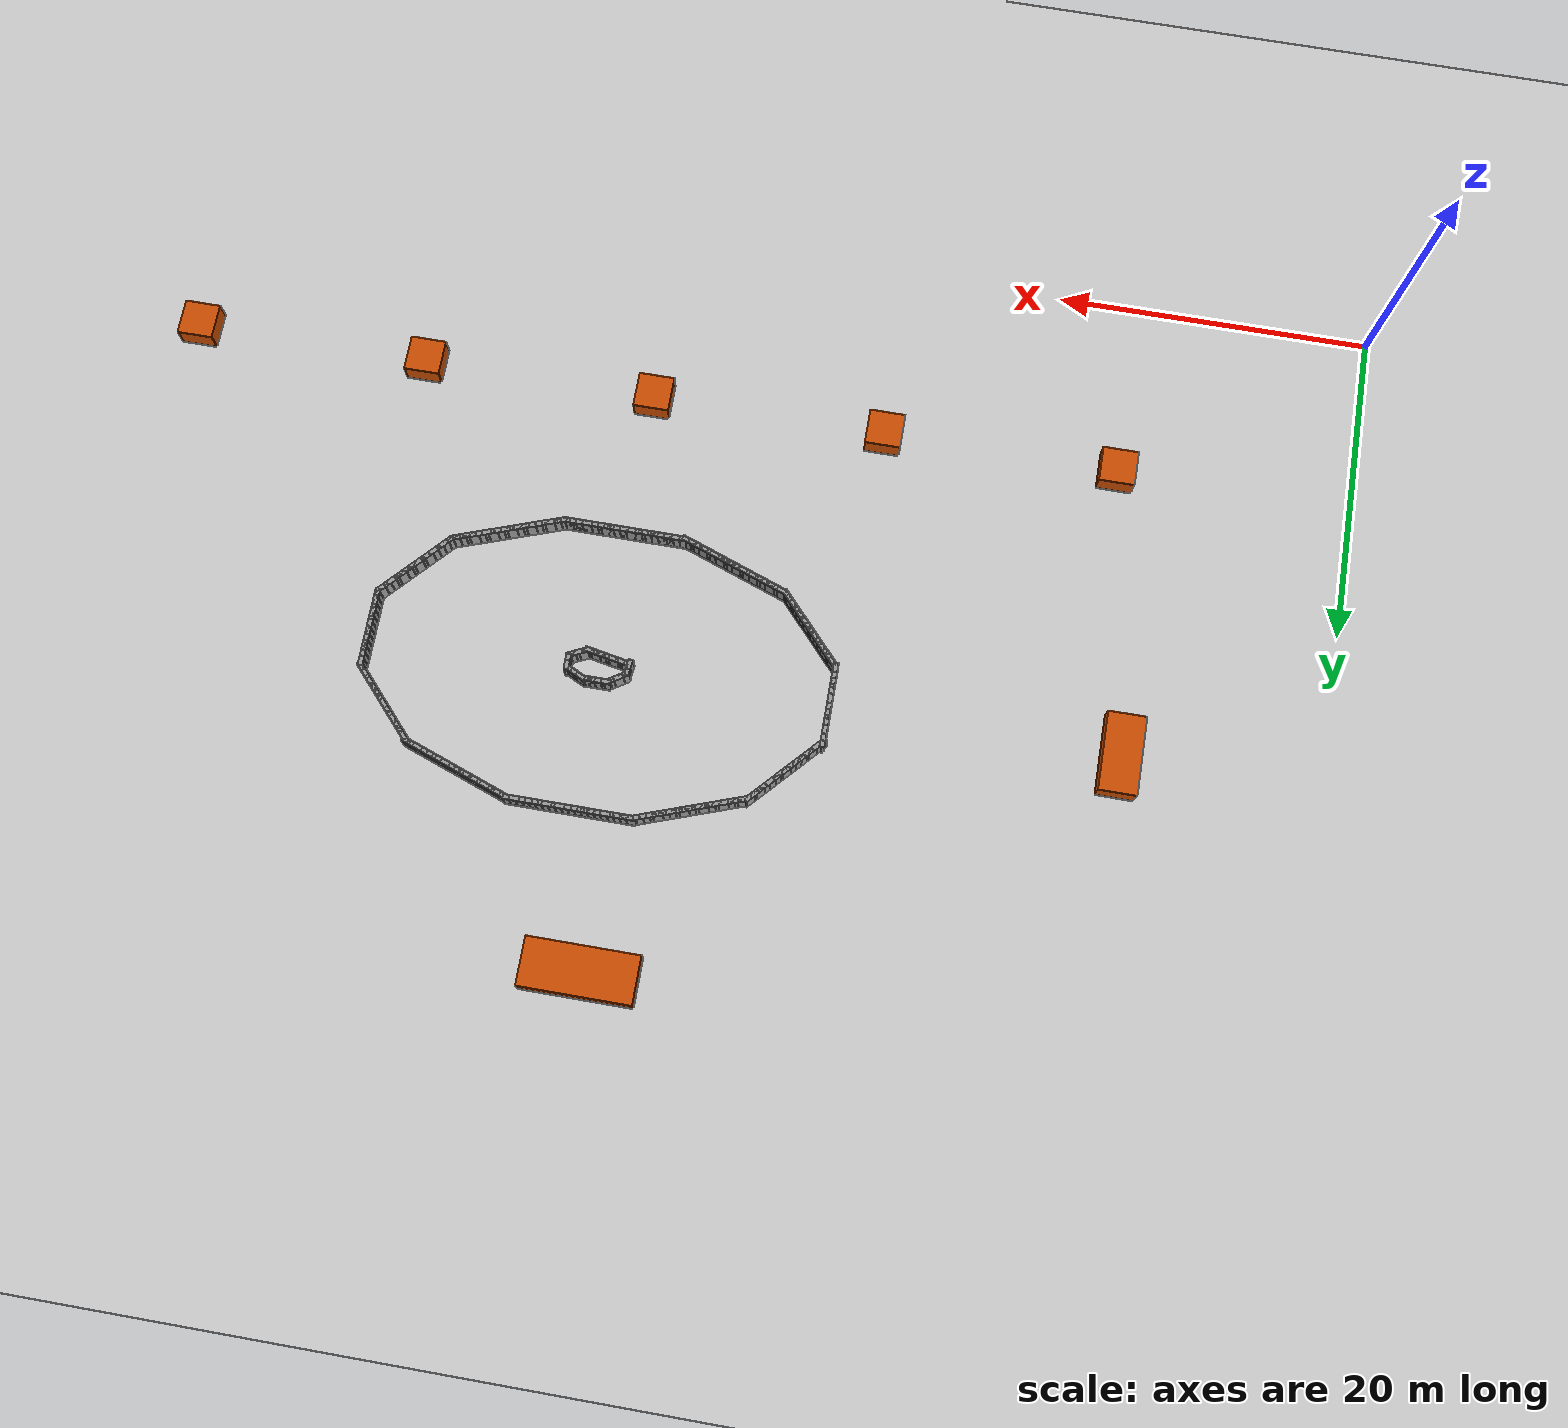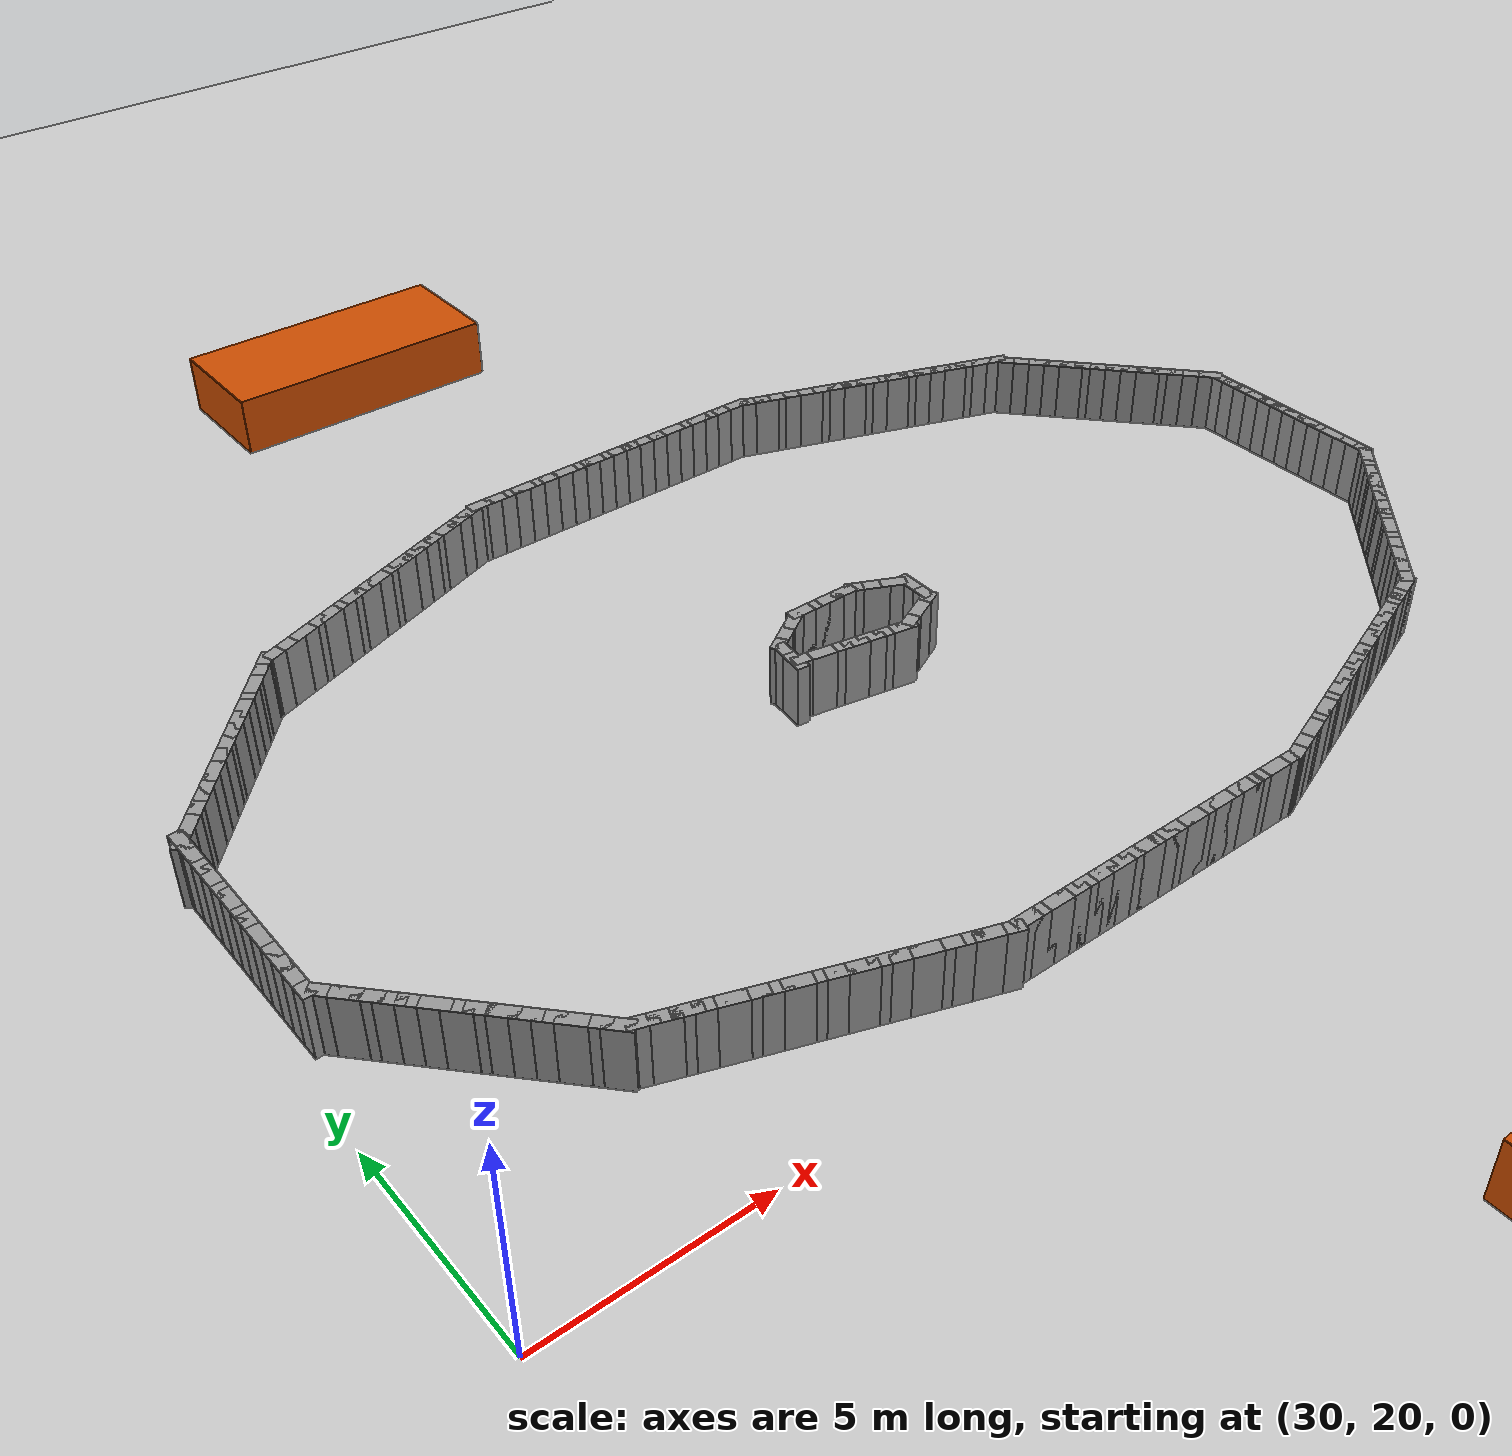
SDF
<?xml version="1.0" ?>
<sdf version="1.5">
  <world name="img_rect_obs">
    <include><uri>model://sun</uri></include>
    <include><uri>model://ground_plane</uri></include>
    <model name="wallL_0">
      <static>true</static>
      <pose>30.569 32.423 0.750 0 0 -1.571</pose>
      <link name="link">
        <collision name="col">
          <geometry><box><size>0.600 0.300 1.500</size></box></geometry>
        </collision>
        <visual name="vis">
          <geometry><box><size>0.600 0.300 1.500</size></box></geometry>
          <material>
            <ambient>0.6 0.6 0.6 1</ambient>
            <diffuse>0.6 0.6 0.6 1</diffuse>
          </material>
        </visual>
      </link>
    </model>
    <model name="wallL_1">
      <static>true</static>
      <pose>30.569 32.023 0.750 0 0 -1.571</pose>
      <link name="link">
        <collision name="col">
          <geometry><box><size>0.600 0.300 1.500</size></box></geometry>
        </collision>
        <visual name="vis">
          <geometry><box><size>0.600 0.300 1.500</size></box></geometry>
          <material>
            <ambient>0.6 0.6 0.6 1</ambient>
            <diffuse>0.6 0.6 0.6 1</diffuse>
          </material>
        </visual>
      </link>
    </model>
    <model name="wallL_2">
      <static>true</static>
      <pose>30.569 31.623 0.750 0 0 -1.571</pose>
      <link name="link">
        <collision name="col">
          <geometry><box><size>0.600 0.300 1.500</size></box></geometry>
        </collision>
        <visual name="vis">
          <geometry><box><size>0.600 0.300 1.500</size></box></geometry>
          <material>
            <ambient>0.6 0.6 0.6 1</ambient>
            <diffuse>0.6 0.6 0.6 1</diffuse>
          </material>
        </visual>
      </link>
    </model>
    <model name="wallL_3">
      <static>true</static>
      <pose>30.569 31.223 0.750 0 0 -1.571</pose>
      <link name="link">
        <collision name="col">
          <geometry><box><size>0.600 0.300 1.500</size></box></geometry>
        </collision>
        <visual name="vis">
          <geometry><box><size>0.600 0.300 1.500</size></box></geometry>
          <material>
            <ambient>0.6 0.6 0.6 1</ambient>
            <diffuse>0.6 0.6 0.6 1</diffuse>
          </material>
        </visual>
      </link>
    </model>
    <model name="wallL_4">
      <static>true</static>
      <pose>30.569 30.823 0.750 0 0 -1.571</pose>
      <link name="link">
        <collision name="col">
          <geometry><box><size>0.600 0.300 1.500</size></box></geometry>
        </collision>
        <visual name="vis">
          <geometry><box><size>0.600 0.300 1.500</size></box></geometry>
          <material>
            <ambient>0.6 0.6 0.6 1</ambient>
            <diffuse>0.6 0.6 0.6 1</diffuse>
          </material>
        </visual>
      </link>
    </model>
    <model name="wallL_5">
      <static>true</static>
      <pose>30.569 30.423 0.750 0 0 -1.571</pose>
      <link name="link">
        <collision name="col">
          <geometry><box><size>0.600 0.300 1.500</size></box></geometry>
        </collision>
        <visual name="vis">
          <geometry><box><size>0.600 0.300 1.500</size></box></geometry>
          <material>
            <ambient>0.6 0.6 0.6 1</ambient>
            <diffuse>0.6 0.6 0.6 1</diffuse>
          </material>
        </visual>
      </link>
    </model>
    <model name="wallL_6">
      <static>true</static>
      <pose>30.569 30.023 0.750 0 0 -1.571</pose>
      <link name="link">
        <collision name="col">
          <geometry><box><size>0.600 0.300 1.500</size></box></geometry>
        </collision>
        <visual name="vis">
          <geometry><box><size>0.600 0.300 1.500</size></box></geometry>
          <material>
            <ambient>0.6 0.6 0.6 1</ambient>
            <diffuse>0.6 0.6 0.6 1</diffuse>
          </material>
        </visual>
      </link>
    </model>
    <model name="wallL_7">
      <static>true</static>
      <pose>30.569 29.623 0.750 0 0 -1.571</pose>
      <link name="link">
        <collision name="col">
          <geometry><box><size>0.600 0.300 1.500</size></box></geometry>
        </collision>
        <visual name="vis">
          <geometry><box><size>0.600 0.300 1.500</size></box></geometry>
          <material>
            <ambient>0.6 0.6 0.6 1</ambient>
            <diffuse>0.6 0.6 0.6 1</diffuse>
          </material>
        </visual>
      </link>
    </model>
    <model name="wallL_8">
      <static>true</static>
      <pose>30.569 29.223 0.750 0 0 -1.571</pose>
      <link name="link">
        <collision name="col">
          <geometry><box><size>0.600 0.300 1.500</size></box></geometry>
        </collision>
        <visual name="vis">
          <geometry><box><size>0.600 0.300 1.500</size></box></geometry>
          <material>
            <ambient>0.6 0.6 0.6 1</ambient>
            <diffuse>0.6 0.6 0.6 1</diffuse>
          </material>
        </visual>
      </link>
    </model>
    <model name="wallL_9">
      <static>true</static>
      <pose>30.569 28.823 0.750 0 0 -1.571</pose>
      <link name="link">
        <collision name="col">
          <geometry><box><size>0.600 0.300 1.500</size></box></geometry>
        </collision>
        <visual name="vis">
          <geometry><box><size>0.600 0.300 1.500</size></box></geometry>
          <material>
            <ambient>0.6 0.6 0.6 1</ambient>
            <diffuse>0.6 0.6 0.6 1</diffuse>
          </material>
        </visual>
      </link>
    </model>
    <model name="wallL_10">
      <static>true</static>
      <pose>30.569 28.423 0.750 0 0 -1.571</pose>
      <link name="link">
        <collision name="col">
          <geometry><box><size>0.600 0.300 1.500</size></box></geometry>
        </collision>
        <visual name="vis">
          <geometry><box><size>0.600 0.300 1.500</size></box></geometry>
          <material>
            <ambient>0.6 0.6 0.6 1</ambient>
            <diffuse>0.6 0.6 0.6 1</diffuse>
          </material>
        </visual>
      </link>
    </model>
    <model name="wallL_11">
      <static>true</static>
      <pose>30.569 28.023 0.750 0 0 -1.571</pose>
      <link name="link">
        <collision name="col">
          <geometry><box><size>0.600 0.300 1.500</size></box></geometry>
        </collision>
        <visual name="vis">
          <geometry><box><size>0.600 0.300 1.500</size></box></geometry>
          <material>
            <ambient>0.6 0.6 0.6 1</ambient>
            <diffuse>0.6 0.6 0.6 1</diffuse>
          </material>
        </visual>
      </link>
    </model>
    <model name="wallL_12">
      <static>true</static>
      <pose>30.569 27.623 0.750 0 0 -1.571</pose>
      <link name="link">
        <collision name="col">
          <geometry><box><size>0.600 0.300 1.500</size></box></geometry>
        </collision>
        <visual name="vis">
          <geometry><box><size>0.600 0.300 1.500</size></box></geometry>
          <material>
            <ambient>0.6 0.6 0.6 1</ambient>
            <diffuse>0.6 0.6 0.6 1</diffuse>
          </material>
        </visual>
      </link>
    </model>
    <model name="wallL_13">
      <static>true</static>
      <pose>30.808 27.316 0.750 0 0 -0.829</pose>
      <link name="link">
        <collision name="col">
          <geometry><box><size>0.600 0.300 1.500</size></box></geometry>
        </collision>
        <visual name="vis">
          <geometry><box><size>0.600 0.300 1.500</size></box></geometry>
          <material>
            <ambient>0.6 0.6 0.6 1</ambient>
            <diffuse>0.6 0.6 0.6 1</diffuse>
          </material>
        </visual>
      </link>
    </model>
    <model name="wallL_14">
      <static>true</static>
      <pose>31.078 27.021 0.750 0 0 -0.829</pose>
      <link name="link">
        <collision name="col">
          <geometry><box><size>0.600 0.300 1.500</size></box></geometry>
        </collision>
        <visual name="vis">
          <geometry><box><size>0.600 0.300 1.500</size></box></geometry>
          <material>
            <ambient>0.6 0.6 0.6 1</ambient>
            <diffuse>0.6 0.6 0.6 1</diffuse>
          </material>
        </visual>
      </link>
    </model>
    <model name="wallL_15">
      <static>true</static>
      <pose>31.349 26.726 0.750 0 0 -0.829</pose>
      <link name="link">
        <collision name="col">
          <geometry><box><size>0.600 0.300 1.500</size></box></geometry>
        </collision>
        <visual name="vis">
          <geometry><box><size>0.600 0.300 1.500</size></box></geometry>
          <material>
            <ambient>0.6 0.6 0.6 1</ambient>
            <diffuse>0.6 0.6 0.6 1</diffuse>
          </material>
        </visual>
      </link>
    </model>
    <model name="wallL_16">
      <static>true</static>
      <pose>31.619 26.431 0.750 0 0 -0.829</pose>
      <link name="link">
        <collision name="col">
          <geometry><box><size>0.600 0.300 1.500</size></box></geometry>
        </collision>
        <visual name="vis">
          <geometry><box><size>0.600 0.300 1.500</size></box></geometry>
          <material>
            <ambient>0.6 0.6 0.6 1</ambient>
            <diffuse>0.6 0.6 0.6 1</diffuse>
          </material>
        </visual>
      </link>
    </model>
    <model name="wallL_17">
      <static>true</static>
      <pose>31.889 26.136 0.750 0 0 -0.829</pose>
      <link name="link">
        <collision name="col">
          <geometry><box><size>0.600 0.300 1.500</size></box></geometry>
        </collision>
        <visual name="vis">
          <geometry><box><size>0.600 0.300 1.500</size></box></geometry>
          <material>
            <ambient>0.6 0.6 0.6 1</ambient>
            <diffuse>0.6 0.6 0.6 1</diffuse>
          </material>
        </visual>
      </link>
    </model>
    <model name="wallL_18">
      <static>true</static>
      <pose>32.159 25.841 0.750 0 0 -0.829</pose>
      <link name="link">
        <collision name="col">
          <geometry><box><size>0.600 0.300 1.500</size></box></geometry>
        </collision>
        <visual name="vis">
          <geometry><box><size>0.600 0.300 1.500</size></box></geometry>
          <material>
            <ambient>0.6 0.6 0.6 1</ambient>
            <diffuse>0.6 0.6 0.6 1</diffuse>
          </material>
        </visual>
      </link>
    </model>
    <model name="wallL_19">
      <static>true</static>
      <pose>32.429 25.546 0.750 0 0 -0.829</pose>
      <link name="link">
        <collision name="col">
          <geometry><box><size>0.600 0.300 1.500</size></box></geometry>
        </collision>
        <visual name="vis">
          <geometry><box><size>0.600 0.300 1.500</size></box></geometry>
          <material>
            <ambient>0.6 0.6 0.6 1</ambient>
            <diffuse>0.6 0.6 0.6 1</diffuse>
          </material>
        </visual>
      </link>
    </model>
    <model name="wallL_20">
      <static>true</static>
      <pose>32.700 25.252 0.750 0 0 -0.829</pose>
      <link name="link">
        <collision name="col">
          <geometry><box><size>0.600 0.300 1.500</size></box></geometry>
        </collision>
        <visual name="vis">
          <geometry><box><size>0.600 0.300 1.500</size></box></geometry>
          <material>
            <ambient>0.6 0.6 0.6 1</ambient>
            <diffuse>0.6 0.6 0.6 1</diffuse>
          </material>
        </visual>
      </link>
    </model>
    <model name="wallL_21">
      <static>true</static>
      <pose>32.970 24.957 0.750 0 0 -0.829</pose>
      <link name="link">
        <collision name="col">
          <geometry><box><size>0.600 0.300 1.500</size></box></geometry>
        </collision>
        <visual name="vis">
          <geometry><box><size>0.600 0.300 1.500</size></box></geometry>
          <material>
            <ambient>0.6 0.6 0.6 1</ambient>
            <diffuse>0.6 0.6 0.6 1</diffuse>
          </material>
        </visual>
      </link>
    </model>
    <model name="wallL_22">
      <static>true</static>
      <pose>33.240 24.662 0.750 0 0 -0.829</pose>
      <link name="link">
        <collision name="col">
          <geometry><box><size>0.600 0.300 1.500</size></box></geometry>
        </collision>
        <visual name="vis">
          <geometry><box><size>0.600 0.300 1.500</size></box></geometry>
          <material>
            <ambient>0.6 0.6 0.6 1</ambient>
            <diffuse>0.6 0.6 0.6 1</diffuse>
          </material>
        </visual>
      </link>
    </model>
    <model name="wallL_23">
      <static>true</static>
      <pose>33.510 24.367 0.750 0 0 -0.829</pose>
      <link name="link">
        <collision name="col">
          <geometry><box><size>0.600 0.300 1.500</size></box></geometry>
        </collision>
        <visual name="vis">
          <geometry><box><size>0.600 0.300 1.500</size></box></geometry>
          <material>
            <ambient>0.6 0.6 0.6 1</ambient>
            <diffuse>0.6 0.6 0.6 1</diffuse>
          </material>
        </visual>
      </link>
    </model>
    <model name="wallL_24">
      <static>true</static>
      <pose>33.780 24.072 0.750 0 0 -0.829</pose>
      <link name="link">
        <collision name="col">
          <geometry><box><size>0.600 0.300 1.500</size></box></geometry>
        </collision>
        <visual name="vis">
          <geometry><box><size>0.600 0.300 1.500</size></box></geometry>
          <material>
            <ambient>0.6 0.6 0.6 1</ambient>
            <diffuse>0.6 0.6 0.6 1</diffuse>
          </material>
        </visual>
      </link>
    </model>
    <model name="wallL_25">
      <static>true</static>
      <pose>34.051 23.777 0.750 0 0 -0.829</pose>
      <link name="link">
        <collision name="col">
          <geometry><box><size>0.600 0.300 1.500</size></box></geometry>
        </collision>
        <visual name="vis">
          <geometry><box><size>0.600 0.300 1.500</size></box></geometry>
          <material>
            <ambient>0.6 0.6 0.6 1</ambient>
            <diffuse>0.6 0.6 0.6 1</diffuse>
          </material>
        </visual>
      </link>
    </model>
    <model name="wallL_26">
      <static>true</static>
      <pose>34.321 23.482 0.750 0 0 -0.829</pose>
      <link name="link">
        <collision name="col">
          <geometry><box><size>0.600 0.300 1.500</size></box></geometry>
        </collision>
        <visual name="vis">
          <geometry><box><size>0.600 0.300 1.500</size></box></geometry>
          <material>
            <ambient>0.6 0.6 0.6 1</ambient>
            <diffuse>0.6 0.6 0.6 1</diffuse>
          </material>
        </visual>
      </link>
    </model>
    <model name="wallL_27">
      <static>true</static>
      <pose>34.662 23.294 0.750 0 0 -0.343</pose>
      <link name="link">
        <collision name="col">
          <geometry><box><size>0.600 0.300 1.500</size></box></geometry>
        </collision>
        <visual name="vis">
          <geometry><box><size>0.600 0.300 1.500</size></box></geometry>
          <material>
            <ambient>0.6 0.6 0.6 1</ambient>
            <diffuse>0.6 0.6 0.6 1</diffuse>
          </material>
        </visual>
      </link>
    </model>
    <model name="wallL_28">
      <static>true</static>
      <pose>35.039 23.159 0.750 0 0 -0.343</pose>
      <link name="link">
        <collision name="col">
          <geometry><box><size>0.600 0.300 1.500</size></box></geometry>
        </collision>
        <visual name="vis">
          <geometry><box><size>0.600 0.300 1.500</size></box></geometry>
          <material>
            <ambient>0.6 0.6 0.6 1</ambient>
            <diffuse>0.6 0.6 0.6 1</diffuse>
          </material>
        </visual>
      </link>
    </model>
    <model name="wallL_29">
      <static>true</static>
      <pose>35.415 23.025 0.750 0 0 -0.343</pose>
      <link name="link">
        <collision name="col">
          <geometry><box><size>0.600 0.300 1.500</size></box></geometry>
        </collision>
        <visual name="vis">
          <geometry><box><size>0.600 0.300 1.500</size></box></geometry>
          <material>
            <ambient>0.6 0.6 0.6 1</ambient>
            <diffuse>0.6 0.6 0.6 1</diffuse>
          </material>
        </visual>
      </link>
    </model>
    <model name="wallL_30">
      <static>true</static>
      <pose>35.792 22.890 0.750 0 0 -0.343</pose>
      <link name="link">
        <collision name="col">
          <geometry><box><size>0.600 0.300 1.500</size></box></geometry>
        </collision>
        <visual name="vis">
          <geometry><box><size>0.600 0.300 1.500</size></box></geometry>
          <material>
            <ambient>0.6 0.6 0.6 1</ambient>
            <diffuse>0.6 0.6 0.6 1</diffuse>
          </material>
        </visual>
      </link>
    </model>
    <model name="wallL_31">
      <static>true</static>
      <pose>36.169 22.755 0.750 0 0 -0.343</pose>
      <link name="link">
        <collision name="col">
          <geometry><box><size>0.600 0.300 1.500</size></box></geometry>
        </collision>
        <visual name="vis">
          <geometry><box><size>0.600 0.300 1.500</size></box></geometry>
          <material>
            <ambient>0.6 0.6 0.6 1</ambient>
            <diffuse>0.6 0.6 0.6 1</diffuse>
          </material>
        </visual>
      </link>
    </model>
    <model name="wallL_32">
      <static>true</static>
      <pose>36.545 22.621 0.750 0 0 -0.343</pose>
      <link name="link">
        <collision name="col">
          <geometry><box><size>0.600 0.300 1.500</size></box></geometry>
        </collision>
        <visual name="vis">
          <geometry><box><size>0.600 0.300 1.500</size></box></geometry>
          <material>
            <ambient>0.6 0.6 0.6 1</ambient>
            <diffuse>0.6 0.6 0.6 1</diffuse>
          </material>
        </visual>
      </link>
    </model>
    <model name="wallL_33">
      <static>true</static>
      <pose>36.922 22.486 0.750 0 0 -0.343</pose>
      <link name="link">
        <collision name="col">
          <geometry><box><size>0.600 0.300 1.500</size></box></geometry>
        </collision>
        <visual name="vis">
          <geometry><box><size>0.600 0.300 1.500</size></box></geometry>
          <material>
            <ambient>0.6 0.6 0.6 1</ambient>
            <diffuse>0.6 0.6 0.6 1</diffuse>
          </material>
        </visual>
      </link>
    </model>
    <model name="wallL_34">
      <static>true</static>
      <pose>37.299 22.351 0.750 0 0 -0.343</pose>
      <link name="link">
        <collision name="col">
          <geometry><box><size>0.600 0.300 1.500</size></box></geometry>
        </collision>
        <visual name="vis">
          <geometry><box><size>0.600 0.300 1.500</size></box></geometry>
          <material>
            <ambient>0.6 0.6 0.6 1</ambient>
            <diffuse>0.6 0.6 0.6 1</diffuse>
          </material>
        </visual>
      </link>
    </model>
    <model name="wallL_35">
      <static>true</static>
      <pose>37.675 22.217 0.750 0 0 -0.343</pose>
      <link name="link">
        <collision name="col">
          <geometry><box><size>0.600 0.300 1.500</size></box></geometry>
        </collision>
        <visual name="vis">
          <geometry><box><size>0.600 0.300 1.500</size></box></geometry>
          <material>
            <ambient>0.6 0.6 0.6 1</ambient>
            <diffuse>0.6 0.6 0.6 1</diffuse>
          </material>
        </visual>
      </link>
    </model>
    <model name="wallL_36">
      <static>true</static>
      <pose>38.052 22.082 0.750 0 0 -0.343</pose>
      <link name="link">
        <collision name="col">
          <geometry><box><size>0.600 0.300 1.500</size></box></geometry>
        </collision>
        <visual name="vis">
          <geometry><box><size>0.600 0.300 1.500</size></box></geometry>
          <material>
            <ambient>0.6 0.6 0.6 1</ambient>
            <diffuse>0.6 0.6 0.6 1</diffuse>
          </material>
        </visual>
      </link>
    </model>
    <model name="wallL_37">
      <static>true</static>
      <pose>38.429 21.947 0.750 0 0 -0.343</pose>
      <link name="link">
        <collision name="col">
          <geometry><box><size>0.600 0.300 1.500</size></box></geometry>
        </collision>
        <visual name="vis">
          <geometry><box><size>0.600 0.300 1.500</size></box></geometry>
          <material>
            <ambient>0.6 0.6 0.6 1</ambient>
            <diffuse>0.6 0.6 0.6 1</diffuse>
          </material>
        </visual>
      </link>
    </model>
    <model name="wallL_38">
      <static>true</static>
      <pose>38.805 21.813 0.750 0 0 -0.343</pose>
      <link name="link">
        <collision name="col">
          <geometry><box><size>0.600 0.300 1.500</size></box></geometry>
        </collision>
        <visual name="vis">
          <geometry><box><size>0.600 0.300 1.500</size></box></geometry>
          <material>
            <ambient>0.6 0.6 0.6 1</ambient>
            <diffuse>0.6 0.6 0.6 1</diffuse>
          </material>
        </visual>
      </link>
    </model>
    <model name="wallL_39">
      <static>true</static>
      <pose>39.182 21.678 0.750 0 0 -0.343</pose>
      <link name="link">
        <collision name="col">
          <geometry><box><size>0.600 0.300 1.500</size></box></geometry>
        </collision>
        <visual name="vis">
          <geometry><box><size>0.600 0.300 1.500</size></box></geometry>
          <material>
            <ambient>0.6 0.6 0.6 1</ambient>
            <diffuse>0.6 0.6 0.6 1</diffuse>
          </material>
        </visual>
      </link>
    </model>
    <model name="wallL_40">
      <static>true</static>
      <pose>39.559 21.543 0.750 0 0 -0.343</pose>
      <link name="link">
        <collision name="col">
          <geometry><box><size>0.600 0.300 1.500</size></box></geometry>
        </collision>
        <visual name="vis">
          <geometry><box><size>0.600 0.300 1.500</size></box></geometry>
          <material>
            <ambient>0.6 0.6 0.6 1</ambient>
            <diffuse>0.6 0.6 0.6 1</diffuse>
          </material>
        </visual>
      </link>
    </model>
    <model name="wallL_41">
      <static>true</static>
      <pose>39.935 21.409 0.750 0 0 -0.343</pose>
      <link name="link">
        <collision name="col">
          <geometry><box><size>0.600 0.300 1.500</size></box></geometry>
        </collision>
        <visual name="vis">
          <geometry><box><size>0.600 0.300 1.500</size></box></geometry>
          <material>
            <ambient>0.6 0.6 0.6 1</ambient>
            <diffuse>0.6 0.6 0.6 1</diffuse>
          </material>
        </visual>
      </link>
    </model>
    <model name="wallL_42">
      <static>true</static>
      <pose>40.312 21.274 0.750 0 0 -0.343</pose>
      <link name="link">
        <collision name="col">
          <geometry><box><size>0.600 0.300 1.500</size></box></geometry>
        </collision>
        <visual name="vis">
          <geometry><box><size>0.600 0.300 1.500</size></box></geometry>
          <material>
            <ambient>0.6 0.6 0.6 1</ambient>
            <diffuse>0.6 0.6 0.6 1</diffuse>
          </material>
        </visual>
      </link>
    </model>
    <model name="wallL_43">
      <static>true</static>
      <pose>40.689 21.139 0.750 0 0 -0.343</pose>
      <link name="link">
        <collision name="col">
          <geometry><box><size>0.600 0.300 1.500</size></box></geometry>
        </collision>
        <visual name="vis">
          <geometry><box><size>0.600 0.300 1.500</size></box></geometry>
          <material>
            <ambient>0.6 0.6 0.6 1</ambient>
            <diffuse>0.6 0.6 0.6 1</diffuse>
          </material>
        </visual>
      </link>
    </model>
    <model name="wallL_44">
      <static>true</static>
      <pose>41.065 21.005 0.750 0 0 -0.343</pose>
      <link name="link">
        <collision name="col">
          <geometry><box><size>0.600 0.300 1.500</size></box></geometry>
        </collision>
        <visual name="vis">
          <geometry><box><size>0.600 0.300 1.500</size></box></geometry>
          <material>
            <ambient>0.6 0.6 0.6 1</ambient>
            <diffuse>0.6 0.6 0.6 1</diffuse>
          </material>
        </visual>
      </link>
    </model>
    <model name="wallL_45">
      <static>true</static>
      <pose>41.462 20.985 0.750 0 0 0.000</pose>
      <link name="link">
        <collision name="col">
          <geometry><box><size>0.600 0.300 1.500</size></box></geometry>
        </collision>
        <visual name="vis">
          <geometry><box><size>0.600 0.300 1.500</size></box></geometry>
          <material>
            <ambient>0.6 0.6 0.6 1</ambient>
            <diffuse>0.6 0.6 0.6 1</diffuse>
          </material>
        </visual>
      </link>
    </model>
    <model name="wallL_46">
      <static>true</static>
      <pose>41.862 20.985 0.750 0 0 0.000</pose>
      <link name="link">
        <collision name="col">
          <geometry><box><size>0.600 0.300 1.500</size></box></geometry>
        </collision>
        <visual name="vis">
          <geometry><box><size>0.600 0.300 1.500</size></box></geometry>
          <material>
            <ambient>0.6 0.6 0.6 1</ambient>
            <diffuse>0.6 0.6 0.6 1</diffuse>
          </material>
        </visual>
      </link>
    </model>
    <model name="wallL_47">
      <static>true</static>
      <pose>42.262 20.985 0.750 0 0 0.000</pose>
      <link name="link">
        <collision name="col">
          <geometry><box><size>0.600 0.300 1.500</size></box></geometry>
        </collision>
        <visual name="vis">
          <geometry><box><size>0.600 0.300 1.500</size></box></geometry>
          <material>
            <ambient>0.6 0.6 0.6 1</ambient>
            <diffuse>0.6 0.6 0.6 1</diffuse>
          </material>
        </visual>
      </link>
    </model>
    <model name="wallL_48">
      <static>true</static>
      <pose>42.662 20.985 0.750 0 0 0.000</pose>
      <link name="link">
        <collision name="col">
          <geometry><box><size>0.600 0.300 1.500</size></box></geometry>
        </collision>
        <visual name="vis">
          <geometry><box><size>0.600 0.300 1.500</size></box></geometry>
          <material>
            <ambient>0.6 0.6 0.6 1</ambient>
            <diffuse>0.6 0.6 0.6 1</diffuse>
          </material>
        </visual>
      </link>
    </model>
    <model name="wallL_49">
      <static>true</static>
      <pose>43.062 20.985 0.750 0 0 0.000</pose>
      <link name="link">
        <collision name="col">
          <geometry><box><size>0.600 0.300 1.500</size></box></geometry>
        </collision>
        <visual name="vis">
          <geometry><box><size>0.600 0.300 1.500</size></box></geometry>
          <material>
            <ambient>0.6 0.6 0.6 1</ambient>
            <diffuse>0.6 0.6 0.6 1</diffuse>
          </material>
        </visual>
      </link>
    </model>
    <model name="wallL_50">
      <static>true</static>
      <pose>43.462 20.985 0.750 0 0 0.000</pose>
      <link name="link">
        <collision name="col">
          <geometry><box><size>0.600 0.300 1.500</size></box></geometry>
        </collision>
        <visual name="vis">
          <geometry><box><size>0.600 0.300 1.500</size></box></geometry>
          <material>
            <ambient>0.6 0.6 0.6 1</ambient>
            <diffuse>0.6 0.6 0.6 1</diffuse>
          </material>
        </visual>
      </link>
    </model>
    <model name="wallL_51">
      <static>true</static>
      <pose>43.862 20.985 0.750 0 0 0.000</pose>
      <link name="link">
        <collision name="col">
          <geometry><box><size>0.600 0.300 1.500</size></box></geometry>
        </collision>
        <visual name="vis">
          <geometry><box><size>0.600 0.300 1.500</size></box></geometry>
          <material>
            <ambient>0.6 0.6 0.6 1</ambient>
            <diffuse>0.6 0.6 0.6 1</diffuse>
          </material>
        </visual>
      </link>
    </model>
    <model name="wallL_52">
      <static>true</static>
      <pose>44.262 20.985 0.750 0 0 0.000</pose>
      <link name="link">
        <collision name="col">
          <geometry><box><size>0.600 0.300 1.500</size></box></geometry>
        </collision>
        <visual name="vis">
          <geometry><box><size>0.600 0.300 1.500</size></box></geometry>
          <material>
            <ambient>0.6 0.6 0.6 1</ambient>
            <diffuse>0.6 0.6 0.6 1</diffuse>
          </material>
        </visual>
      </link>
    </model>
    <model name="wallL_53">
      <static>true</static>
      <pose>44.662 20.985 0.750 0 0 0.000</pose>
      <link name="link">
        <collision name="col">
          <geometry><box><size>0.600 0.300 1.500</size></box></geometry>
        </collision>
        <visual name="vis">
          <geometry><box><size>0.600 0.300 1.500</size></box></geometry>
          <material>
            <ambient>0.6 0.6 0.6 1</ambient>
            <diffuse>0.6 0.6 0.6 1</diffuse>
          </material>
        </visual>
      </link>
    </model>
    <model name="wallL_54">
      <static>true</static>
      <pose>45.062 20.985 0.750 0 0 0.000</pose>
      <link name="link">
        <collision name="col">
          <geometry><box><size>0.600 0.300 1.500</size></box></geometry>
        </collision>
        <visual name="vis">
          <geometry><box><size>0.600 0.300 1.500</size></box></geometry>
          <material>
            <ambient>0.6 0.6 0.6 1</ambient>
            <diffuse>0.6 0.6 0.6 1</diffuse>
          </material>
        </visual>
      </link>
    </model>
    <model name="wallL_55">
      <static>true</static>
      <pose>45.462 20.985 0.750 0 0 0.000</pose>
      <link name="link">
        <collision name="col">
          <geometry><box><size>0.600 0.300 1.500</size></box></geometry>
        </collision>
        <visual name="vis">
          <geometry><box><size>0.600 0.300 1.500</size></box></geometry>
          <material>
            <ambient>0.6 0.6 0.6 1</ambient>
            <diffuse>0.6 0.6 0.6 1</diffuse>
          </material>
        </visual>
      </link>
    </model>
    <model name="wallL_56">
      <static>true</static>
      <pose>45.862 20.985 0.750 0 0 0.000</pose>
      <link name="link">
        <collision name="col">
          <geometry><box><size>0.600 0.300 1.500</size></box></geometry>
        </collision>
        <visual name="vis">
          <geometry><box><size>0.600 0.300 1.500</size></box></geometry>
          <material>
            <ambient>0.6 0.6 0.6 1</ambient>
            <diffuse>0.6 0.6 0.6 1</diffuse>
          </material>
        </visual>
      </link>
    </model>
    <model name="wallL_57">
      <static>true</static>
      <pose>46.262 20.985 0.750 0 0 0.000</pose>
      <link name="link">
        <collision name="col">
          <geometry><box><size>0.600 0.300 1.500</size></box></geometry>
        </collision>
        <visual name="vis">
          <geometry><box><size>0.600 0.300 1.500</size></box></geometry>
          <material>
            <ambient>0.6 0.6 0.6 1</ambient>
            <diffuse>0.6 0.6 0.6 1</diffuse>
          </material>
        </visual>
      </link>
    </model>
    <model name="wallL_58">
      <static>true</static>
      <pose>46.662 20.985 0.750 0 0 0.000</pose>
      <link name="link">
        <collision name="col">
          <geometry><box><size>0.600 0.300 1.500</size></box></geometry>
        </collision>
        <visual name="vis">
          <geometry><box><size>0.600 0.300 1.500</size></box></geometry>
          <material>
            <ambient>0.6 0.6 0.6 1</ambient>
            <diffuse>0.6 0.6 0.6 1</diffuse>
          </material>
        </visual>
      </link>
    </model>
    <model name="wallL_59">
      <static>true</static>
      <pose>47.062 20.985 0.750 0 0 0.000</pose>
      <link name="link">
        <collision name="col">
          <geometry><box><size>0.600 0.300 1.500</size></box></geometry>
        </collision>
        <visual name="vis">
          <geometry><box><size>0.600 0.300 1.500</size></box></geometry>
          <material>
            <ambient>0.6 0.6 0.6 1</ambient>
            <diffuse>0.6 0.6 0.6 1</diffuse>
          </material>
        </visual>
      </link>
    </model>
    <model name="wallL_60">
      <static>true</static>
      <pose>47.462 20.985 0.750 0 0 0.000</pose>
      <link name="link">
        <collision name="col">
          <geometry><box><size>0.600 0.300 1.500</size></box></geometry>
        </collision>
        <visual name="vis">
          <geometry><box><size>0.600 0.300 1.500</size></box></geometry>
          <material>
            <ambient>0.6 0.6 0.6 1</ambient>
            <diffuse>0.6 0.6 0.6 1</diffuse>
          </material>
        </visual>
      </link>
    </model>
    <model name="wallL_61">
      <static>true</static>
      <pose>47.862 20.985 0.750 0 0 0.000</pose>
      <link name="link">
        <collision name="col">
          <geometry><box><size>0.600 0.300 1.500</size></box></geometry>
        </collision>
        <visual name="vis">
          <geometry><box><size>0.600 0.300 1.500</size></box></geometry>
          <material>
            <ambient>0.6 0.6 0.6 1</ambient>
            <diffuse>0.6 0.6 0.6 1</diffuse>
          </material>
        </visual>
      </link>
    </model>
    <model name="wallL_62">
      <static>true</static>
      <pose>48.262 20.985 0.750 0 0 0.000</pose>
      <link name="link">
        <collision name="col">
          <geometry><box><size>0.600 0.300 1.500</size></box></geometry>
        </collision>
        <visual name="vis">
          <geometry><box><size>0.600 0.300 1.500</size></box></geometry>
          <material>
            <ambient>0.6 0.6 0.6 1</ambient>
            <diffuse>0.6 0.6 0.6 1</diffuse>
          </material>
        </visual>
      </link>
    </model>
    <model name="wallL_63">
      <static>true</static>
      <pose>48.662 20.985 0.750 0 0 0.000</pose>
      <link name="link">
        <collision name="col">
          <geometry><box><size>0.600 0.300 1.500</size></box></geometry>
        </collision>
        <visual name="vis">
          <geometry><box><size>0.600 0.300 1.500</size></box></geometry>
          <material>
            <ambient>0.6 0.6 0.6 1</ambient>
            <diffuse>0.6 0.6 0.6 1</diffuse>
          </material>
        </visual>
      </link>
    </model>
    <model name="wallL_64">
      <static>true</static>
      <pose>49.051 21.046 0.750 0 0 0.343</pose>
      <link name="link">
        <collision name="col">
          <geometry><box><size>0.600 0.300 1.500</size></box></geometry>
        </collision>
        <visual name="vis">
          <geometry><box><size>0.600 0.300 1.500</size></box></geometry>
          <material>
            <ambient>0.6 0.6 0.6 1</ambient>
            <diffuse>0.6 0.6 0.6 1</diffuse>
          </material>
        </visual>
      </link>
    </model>
    <model name="wallL_65">
      <static>true</static>
      <pose>49.428 21.181 0.750 0 0 0.343</pose>
      <link name="link">
        <collision name="col">
          <geometry><box><size>0.600 0.300 1.500</size></box></geometry>
        </collision>
        <visual name="vis">
          <geometry><box><size>0.600 0.300 1.500</size></box></geometry>
          <material>
            <ambient>0.6 0.6 0.6 1</ambient>
            <diffuse>0.6 0.6 0.6 1</diffuse>
          </material>
        </visual>
      </link>
    </model>
    <model name="wallL_66">
      <static>true</static>
      <pose>49.804 21.316 0.750 0 0 0.343</pose>
      <link name="link">
        <collision name="col">
          <geometry><box><size>0.600 0.300 1.500</size></box></geometry>
        </collision>
        <visual name="vis">
          <geometry><box><size>0.600 0.300 1.500</size></box></geometry>
          <material>
            <ambient>0.6 0.6 0.6 1</ambient>
            <diffuse>0.6 0.6 0.6 1</diffuse>
          </material>
        </visual>
      </link>
    </model>
    <model name="wallL_67">
      <static>true</static>
      <pose>50.181 21.450 0.750 0 0 0.343</pose>
      <link name="link">
        <collision name="col">
          <geometry><box><size>0.600 0.300 1.500</size></box></geometry>
        </collision>
        <visual name="vis">
          <geometry><box><size>0.600 0.300 1.500</size></box></geometry>
          <material>
            <ambient>0.6 0.6 0.6 1</ambient>
            <diffuse>0.6 0.6 0.6 1</diffuse>
          </material>
        </visual>
      </link>
    </model>
    <model name="wallL_68">
      <static>true</static>
      <pose>50.558 21.585 0.750 0 0 0.343</pose>
      <link name="link">
        <collision name="col">
          <geometry><box><size>0.600 0.300 1.500</size></box></geometry>
        </collision>
        <visual name="vis">
          <geometry><box><size>0.600 0.300 1.500</size></box></geometry>
          <material>
            <ambient>0.6 0.6 0.6 1</ambient>
            <diffuse>0.6 0.6 0.6 1</diffuse>
          </material>
        </visual>
      </link>
    </model>
    <model name="wallL_69">
      <static>true</static>
      <pose>50.934 21.720 0.750 0 0 0.343</pose>
      <link name="link">
        <collision name="col">
          <geometry><box><size>0.600 0.300 1.500</size></box></geometry>
        </collision>
        <visual name="vis">
          <geometry><box><size>0.600 0.300 1.500</size></box></geometry>
          <material>
            <ambient>0.6 0.6 0.6 1</ambient>
            <diffuse>0.6 0.6 0.6 1</diffuse>
          </material>
        </visual>
      </link>
    </model>
    <model name="wallL_70">
      <static>true</static>
      <pose>51.311 21.854 0.750 0 0 0.343</pose>
      <link name="link">
        <collision name="col">
          <geometry><box><size>0.600 0.300 1.500</size></box></geometry>
        </collision>
        <visual name="vis">
          <geometry><box><size>0.600 0.300 1.500</size></box></geometry>
          <material>
            <ambient>0.6 0.6 0.6 1</ambient>
            <diffuse>0.6 0.6 0.6 1</diffuse>
          </material>
        </visual>
      </link>
    </model>
    <model name="wallL_71">
      <static>true</static>
      <pose>51.688 21.989 0.750 0 0 0.343</pose>
      <link name="link">
        <collision name="col">
          <geometry><box><size>0.600 0.300 1.500</size></box></geometry>
        </collision>
        <visual name="vis">
          <geometry><box><size>0.600 0.300 1.500</size></box></geometry>
          <material>
            <ambient>0.6 0.6 0.6 1</ambient>
            <diffuse>0.6 0.6 0.6 1</diffuse>
          </material>
        </visual>
      </link>
    </model>
    <model name="wallL_72">
      <static>true</static>
      <pose>52.064 22.124 0.750 0 0 0.343</pose>
      <link name="link">
        <collision name="col">
          <geometry><box><size>0.600 0.300 1.500</size></box></geometry>
        </collision>
        <visual name="vis">
          <geometry><box><size>0.600 0.300 1.500</size></box></geometry>
          <material>
            <ambient>0.6 0.6 0.6 1</ambient>
            <diffuse>0.6 0.6 0.6 1</diffuse>
          </material>
        </visual>
      </link>
    </model>
    <model name="wallL_73">
      <static>true</static>
      <pose>52.441 22.258 0.750 0 0 0.343</pose>
      <link name="link">
        <collision name="col">
          <geometry><box><size>0.600 0.300 1.500</size></box></geometry>
        </collision>
        <visual name="vis">
          <geometry><box><size>0.600 0.300 1.500</size></box></geometry>
          <material>
            <ambient>0.6 0.6 0.6 1</ambient>
            <diffuse>0.6 0.6 0.6 1</diffuse>
          </material>
        </visual>
      </link>
    </model>
    <model name="wallL_74">
      <static>true</static>
      <pose>52.818 22.393 0.750 0 0 0.343</pose>
      <link name="link">
        <collision name="col">
          <geometry><box><size>0.600 0.300 1.500</size></box></geometry>
        </collision>
        <visual name="vis">
          <geometry><box><size>0.600 0.300 1.500</size></box></geometry>
          <material>
            <ambient>0.6 0.6 0.6 1</ambient>
            <diffuse>0.6 0.6 0.6 1</diffuse>
          </material>
        </visual>
      </link>
    </model>
    <model name="wallL_75">
      <static>true</static>
      <pose>53.194 22.528 0.750 0 0 0.343</pose>
      <link name="link">
        <collision name="col">
          <geometry><box><size>0.600 0.300 1.500</size></box></geometry>
        </collision>
        <visual name="vis">
          <geometry><box><size>0.600 0.300 1.500</size></box></geometry>
          <material>
            <ambient>0.6 0.6 0.6 1</ambient>
            <diffuse>0.6 0.6 0.6 1</diffuse>
          </material>
        </visual>
      </link>
    </model>
    <model name="wallL_76">
      <static>true</static>
      <pose>53.571 22.662 0.750 0 0 0.343</pose>
      <link name="link">
        <collision name="col">
          <geometry><box><size>0.600 0.300 1.500</size></box></geometry>
        </collision>
        <visual name="vis">
          <geometry><box><size>0.600 0.300 1.500</size></box></geometry>
          <material>
            <ambient>0.6 0.6 0.6 1</ambient>
            <diffuse>0.6 0.6 0.6 1</diffuse>
          </material>
        </visual>
      </link>
    </model>
    <model name="wallL_77">
      <static>true</static>
      <pose>53.947 22.797 0.750 0 0 0.343</pose>
      <link name="link">
        <collision name="col">
          <geometry><box><size>0.600 0.300 1.500</size></box></geometry>
        </collision>
        <visual name="vis">
          <geometry><box><size>0.600 0.300 1.500</size></box></geometry>
          <material>
            <ambient>0.6 0.6 0.6 1</ambient>
            <diffuse>0.6 0.6 0.6 1</diffuse>
          </material>
        </visual>
      </link>
    </model>
    <model name="wallL_78">
      <static>true</static>
      <pose>54.324 22.932 0.750 0 0 0.343</pose>
      <link name="link">
        <collision name="col">
          <geometry><box><size>0.600 0.300 1.500</size></box></geometry>
        </collision>
        <visual name="vis">
          <geometry><box><size>0.600 0.300 1.500</size></box></geometry>
          <material>
            <ambient>0.6 0.6 0.6 1</ambient>
            <diffuse>0.6 0.6 0.6 1</diffuse>
          </material>
        </visual>
      </link>
    </model>
    <model name="wallL_79">
      <static>true</static>
      <pose>54.701 23.066 0.750 0 0 0.343</pose>
      <link name="link">
        <collision name="col">
          <geometry><box><size>0.600 0.300 1.500</size></box></geometry>
        </collision>
        <visual name="vis">
          <geometry><box><size>0.600 0.300 1.500</size></box></geometry>
          <material>
            <ambient>0.6 0.6 0.6 1</ambient>
            <diffuse>0.6 0.6 0.6 1</diffuse>
          </material>
        </visual>
      </link>
    </model>
    <model name="wallL_80">
      <static>true</static>
      <pose>55.077 23.201 0.750 0 0 0.343</pose>
      <link name="link">
        <collision name="col">
          <geometry><box><size>0.600 0.300 1.500</size></box></geometry>
        </collision>
        <visual name="vis">
          <geometry><box><size>0.600 0.300 1.500</size></box></geometry>
          <material>
            <ambient>0.6 0.6 0.6 1</ambient>
            <diffuse>0.6 0.6 0.6 1</diffuse>
          </material>
        </visual>
      </link>
    </model>
    <model name="wallL_81">
      <static>true</static>
      <pose>55.454 23.336 0.750 0 0 0.343</pose>
      <link name="link">
        <collision name="col">
          <geometry><box><size>0.600 0.300 1.500</size></box></geometry>
        </collision>
        <visual name="vis">
          <geometry><box><size>0.600 0.300 1.500</size></box></geometry>
          <material>
            <ambient>0.6 0.6 0.6 1</ambient>
            <diffuse>0.6 0.6 0.6 1</diffuse>
          </material>
        </visual>
      </link>
    </model>
    <model name="wallL_82">
      <static>true</static>
      <pose>55.763 23.573 0.750 0 0 0.829</pose>
      <link name="link">
        <collision name="col">
          <geometry><box><size>0.600 0.300 1.500</size></box></geometry>
        </collision>
        <visual name="vis">
          <geometry><box><size>0.600 0.300 1.500</size></box></geometry>
          <material>
            <ambient>0.6 0.6 0.6 1</ambient>
            <diffuse>0.6 0.6 0.6 1</diffuse>
          </material>
        </visual>
      </link>
    </model>
    <model name="wallL_83">
      <static>true</static>
      <pose>56.033 23.868 0.750 0 0 0.829</pose>
      <link name="link">
        <collision name="col">
          <geometry><box><size>0.600 0.300 1.500</size></box></geometry>
        </collision>
        <visual name="vis">
          <geometry><box><size>0.600 0.300 1.500</size></box></geometry>
          <material>
            <ambient>0.6 0.6 0.6 1</ambient>
            <diffuse>0.6 0.6 0.6 1</diffuse>
          </material>
        </visual>
      </link>
    </model>
    <model name="wallL_84">
      <static>true</static>
      <pose>56.303 24.163 0.750 0 0 0.829</pose>
      <link name="link">
        <collision name="col">
          <geometry><box><size>0.600 0.300 1.500</size></box></geometry>
        </collision>
        <visual name="vis">
          <geometry><box><size>0.600 0.300 1.500</size></box></geometry>
          <material>
            <ambient>0.6 0.6 0.6 1</ambient>
            <diffuse>0.6 0.6 0.6 1</diffuse>
          </material>
        </visual>
      </link>
    </model>
    <model name="wallL_85">
      <static>true</static>
      <pose>56.573 24.458 0.750 0 0 0.829</pose>
      <link name="link">
        <collision name="col">
          <geometry><box><size>0.600 0.300 1.500</size></box></geometry>
        </collision>
        <visual name="vis">
          <geometry><box><size>0.600 0.300 1.500</size></box></geometry>
          <material>
            <ambient>0.6 0.6 0.6 1</ambient>
            <diffuse>0.6 0.6 0.6 1</diffuse>
          </material>
        </visual>
      </link>
    </model>
    <model name="wallL_86">
      <static>true</static>
      <pose>56.843 24.753 0.750 0 0 0.829</pose>
      <link name="link">
        <collision name="col">
          <geometry><box><size>0.600 0.300 1.500</size></box></geometry>
        </collision>
        <visual name="vis">
          <geometry><box><size>0.600 0.300 1.500</size></box></geometry>
          <material>
            <ambient>0.6 0.6 0.6 1</ambient>
            <diffuse>0.6 0.6 0.6 1</diffuse>
          </material>
        </visual>
      </link>
    </model>
    <model name="wallL_87">
      <static>true</static>
      <pose>57.114 25.048 0.750 0 0 0.829</pose>
      <link name="link">
        <collision name="col">
          <geometry><box><size>0.600 0.300 1.500</size></box></geometry>
        </collision>
        <visual name="vis">
          <geometry><box><size>0.600 0.300 1.500</size></box></geometry>
          <material>
            <ambient>0.6 0.6 0.6 1</ambient>
            <diffuse>0.6 0.6 0.6 1</diffuse>
          </material>
        </visual>
      </link>
    </model>
    <model name="wallL_88">
      <static>true</static>
      <pose>57.384 25.343 0.750 0 0 0.829</pose>
      <link name="link">
        <collision name="col">
          <geometry><box><size>0.600 0.300 1.500</size></box></geometry>
        </collision>
        <visual name="vis">
          <geometry><box><size>0.600 0.300 1.500</size></box></geometry>
          <material>
            <ambient>0.6 0.6 0.6 1</ambient>
            <diffuse>0.6 0.6 0.6 1</diffuse>
          </material>
        </visual>
      </link>
    </model>
    <model name="wallL_89">
      <static>true</static>
      <pose>57.654 25.637 0.750 0 0 0.829</pose>
      <link name="link">
        <collision name="col">
          <geometry><box><size>0.600 0.300 1.500</size></box></geometry>
        </collision>
        <visual name="vis">
          <geometry><box><size>0.600 0.300 1.500</size></box></geometry>
          <material>
            <ambient>0.6 0.6 0.6 1</ambient>
            <diffuse>0.6 0.6 0.6 1</diffuse>
          </material>
        </visual>
      </link>
    </model>
    <model name="wallL_90">
      <static>true</static>
      <pose>57.924 25.932 0.750 0 0 0.829</pose>
      <link name="link">
        <collision name="col">
          <geometry><box><size>0.600 0.300 1.500</size></box></geometry>
        </collision>
        <visual name="vis">
          <geometry><box><size>0.600 0.300 1.500</size></box></geometry>
          <material>
            <ambient>0.6 0.6 0.6 1</ambient>
            <diffuse>0.6 0.6 0.6 1</diffuse>
          </material>
        </visual>
      </link>
    </model>
    <model name="wallL_91">
      <static>true</static>
      <pose>58.194 26.227 0.750 0 0 0.829</pose>
      <link name="link">
        <collision name="col">
          <geometry><box><size>0.600 0.300 1.500</size></box></geometry>
        </collision>
        <visual name="vis">
          <geometry><box><size>0.600 0.300 1.500</size></box></geometry>
          <material>
            <ambient>0.6 0.6 0.6 1</ambient>
            <diffuse>0.6 0.6 0.6 1</diffuse>
          </material>
        </visual>
      </link>
    </model>
    <model name="wallL_92">
      <static>true</static>
      <pose>58.465 26.522 0.750 0 0 0.829</pose>
      <link name="link">
        <collision name="col">
          <geometry><box><size>0.600 0.300 1.500</size></box></geometry>
        </collision>
        <visual name="vis">
          <geometry><box><size>0.600 0.300 1.500</size></box></geometry>
          <material>
            <ambient>0.6 0.6 0.6 1</ambient>
            <diffuse>0.6 0.6 0.6 1</diffuse>
          </material>
        </visual>
      </link>
    </model>
    <model name="wallL_93">
      <static>true</static>
      <pose>58.735 26.817 0.750 0 0 0.829</pose>
      <link name="link">
        <collision name="col">
          <geometry><box><size>0.600 0.300 1.500</size></box></geometry>
        </collision>
        <visual name="vis">
          <geometry><box><size>0.600 0.300 1.500</size></box></geometry>
          <material>
            <ambient>0.6 0.6 0.6 1</ambient>
            <diffuse>0.6 0.6 0.6 1</diffuse>
          </material>
        </visual>
      </link>
    </model>
    <model name="wallL_94">
      <static>true</static>
      <pose>59.005 27.112 0.750 0 0 0.829</pose>
      <link name="link">
        <collision name="col">
          <geometry><box><size>0.600 0.300 1.500</size></box></geometry>
        </collision>
        <visual name="vis">
          <geometry><box><size>0.600 0.300 1.500</size></box></geometry>
          <material>
            <ambient>0.6 0.6 0.6 1</ambient>
            <diffuse>0.6 0.6 0.6 1</diffuse>
          </material>
        </visual>
      </link>
    </model>
    <model name="wallL_95">
      <static>true</static>
      <pose>59.275 27.407 0.750 0 0 0.829</pose>
      <link name="link">
        <collision name="col">
          <geometry><box><size>0.600 0.300 1.500</size></box></geometry>
        </collision>
        <visual name="vis">
          <geometry><box><size>0.600 0.300 1.500</size></box></geometry>
          <material>
            <ambient>0.6 0.6 0.6 1</ambient>
            <diffuse>0.6 0.6 0.6 1</diffuse>
          </material>
        </visual>
      </link>
    </model>
    <model name="wallL_96">
      <static>true</static>
      <pose>59.431 27.747 0.750 0 0 1.571</pose>
      <link name="link">
        <collision name="col">
          <geometry><box><size>0.600 0.300 1.500</size></box></geometry>
        </collision>
        <visual name="vis">
          <geometry><box><size>0.600 0.300 1.500</size></box></geometry>
          <material>
            <ambient>0.6 0.6 0.6 1</ambient>
            <diffuse>0.6 0.6 0.6 1</diffuse>
          </material>
        </visual>
      </link>
    </model>
    <model name="wallL_97">
      <static>true</static>
      <pose>59.431 28.147 0.750 0 0 1.571</pose>
      <link name="link">
        <collision name="col">
          <geometry><box><size>0.600 0.300 1.500</size></box></geometry>
        </collision>
        <visual name="vis">
          <geometry><box><size>0.600 0.300 1.500</size></box></geometry>
          <material>
            <ambient>0.6 0.6 0.6 1</ambient>
            <diffuse>0.6 0.6 0.6 1</diffuse>
          </material>
        </visual>
      </link>
    </model>
    <model name="wallL_98">
      <static>true</static>
      <pose>59.431 28.547 0.750 0 0 1.571</pose>
      <link name="link">
        <collision name="col">
          <geometry><box><size>0.600 0.300 1.500</size></box></geometry>
        </collision>
        <visual name="vis">
          <geometry><box><size>0.600 0.300 1.500</size></box></geometry>
          <material>
            <ambient>0.6 0.6 0.6 1</ambient>
            <diffuse>0.6 0.6 0.6 1</diffuse>
          </material>
        </visual>
      </link>
    </model>
    <model name="wallL_99">
      <static>true</static>
      <pose>59.431 28.947 0.750 0 0 1.571</pose>
      <link name="link">
        <collision name="col">
          <geometry><box><size>0.600 0.300 1.500</size></box></geometry>
        </collision>
        <visual name="vis">
          <geometry><box><size>0.600 0.300 1.500</size></box></geometry>
          <material>
            <ambient>0.6 0.6 0.6 1</ambient>
            <diffuse>0.6 0.6 0.6 1</diffuse>
          </material>
        </visual>
      </link>
    </model>
    <model name="wallL_100">
      <static>true</static>
      <pose>59.431 29.347 0.750 0 0 1.571</pose>
      <link name="link">
        <collision name="col">
          <geometry><box><size>0.600 0.300 1.500</size></box></geometry>
        </collision>
        <visual name="vis">
          <geometry><box><size>0.600 0.300 1.500</size></box></geometry>
          <material>
            <ambient>0.6 0.6 0.6 1</ambient>
            <diffuse>0.6 0.6 0.6 1</diffuse>
          </material>
        </visual>
      </link>
    </model>
    <model name="wallL_101">
      <static>true</static>
      <pose>59.431 29.747 0.750 0 0 1.571</pose>
      <link name="link">
        <collision name="col">
          <geometry><box><size>0.600 0.300 1.500</size></box></geometry>
        </collision>
        <visual name="vis">
          <geometry><box><size>0.600 0.300 1.500</size></box></geometry>
          <material>
            <ambient>0.6 0.6 0.6 1</ambient>
            <diffuse>0.6 0.6 0.6 1</diffuse>
          </material>
        </visual>
      </link>
    </model>
    <model name="wallL_102">
      <static>true</static>
      <pose>59.431 30.147 0.750 0 0 1.571</pose>
      <link name="link">
        <collision name="col">
          <geometry><box><size>0.600 0.300 1.500</size></box></geometry>
        </collision>
        <visual name="vis">
          <geometry><box><size>0.600 0.300 1.500</size></box></geometry>
          <material>
            <ambient>0.6 0.6 0.6 1</ambient>
            <diffuse>0.6 0.6 0.6 1</diffuse>
          </material>
        </visual>
      </link>
    </model>
    <model name="wallL_103">
      <static>true</static>
      <pose>59.431 30.547 0.750 0 0 1.571</pose>
      <link name="link">
        <collision name="col">
          <geometry><box><size>0.600 0.300 1.500</size></box></geometry>
        </collision>
        <visual name="vis">
          <geometry><box><size>0.600 0.300 1.500</size></box></geometry>
          <material>
            <ambient>0.6 0.6 0.6 1</ambient>
            <diffuse>0.6 0.6 0.6 1</diffuse>
          </material>
        </visual>
      </link>
    </model>
    <model name="wallL_104">
      <static>true</static>
      <pose>59.431 30.947 0.750 0 0 1.571</pose>
      <link name="link">
        <collision name="col">
          <geometry><box><size>0.600 0.300 1.500</size></box></geometry>
        </collision>
        <visual name="vis">
          <geometry><box><size>0.600 0.300 1.500</size></box></geometry>
          <material>
            <ambient>0.6 0.6 0.6 1</ambient>
            <diffuse>0.6 0.6 0.6 1</diffuse>
          </material>
        </visual>
      </link>
    </model>
    <model name="wallL_105">
      <static>true</static>
      <pose>59.431 31.347 0.750 0 0 1.571</pose>
      <link name="link">
        <collision name="col">
          <geometry><box><size>0.600 0.300 1.500</size></box></geometry>
        </collision>
        <visual name="vis">
          <geometry><box><size>0.600 0.300 1.500</size></box></geometry>
          <material>
            <ambient>0.6 0.6 0.6 1</ambient>
            <diffuse>0.6 0.6 0.6 1</diffuse>
          </material>
        </visual>
      </link>
    </model>
    <model name="wallL_106">
      <static>true</static>
      <pose>59.431 31.747 0.750 0 0 1.571</pose>
      <link name="link">
        <collision name="col">
          <geometry><box><size>0.600 0.300 1.500</size></box></geometry>
        </collision>
        <visual name="vis">
          <geometry><box><size>0.600 0.300 1.500</size></box></geometry>
          <material>
            <ambient>0.6 0.6 0.6 1</ambient>
            <diffuse>0.6 0.6 0.6 1</diffuse>
          </material>
        </visual>
      </link>
    </model>
    <model name="wallL_107">
      <static>true</static>
      <pose>59.431 32.147 0.750 0 0 1.571</pose>
      <link name="link">
        <collision name="col">
          <geometry><box><size>0.600 0.300 1.500</size></box></geometry>
        </collision>
        <visual name="vis">
          <geometry><box><size>0.600 0.300 1.500</size></box></geometry>
          <material>
            <ambient>0.6 0.6 0.6 1</ambient>
            <diffuse>0.6 0.6 0.6 1</diffuse>
          </material>
        </visual>
      </link>
    </model>
    <model name="wallL_108">
      <static>true</static>
      <pose>59.347 32.514 0.750 0 0 2.312</pose>
      <link name="link">
        <collision name="col">
          <geometry><box><size>0.600 0.300 1.500</size></box></geometry>
        </collision>
        <visual name="vis">
          <geometry><box><size>0.600 0.300 1.500</size></box></geometry>
          <material>
            <ambient>0.6 0.6 0.6 1</ambient>
            <diffuse>0.6 0.6 0.6 1</diffuse>
          </material>
        </visual>
      </link>
    </model>
    <model name="wallL_109">
      <static>true</static>
      <pose>59.077 32.809 0.750 0 0 2.312</pose>
      <link name="link">
        <collision name="col">
          <geometry><box><size>0.600 0.300 1.500</size></box></geometry>
        </collision>
        <visual name="vis">
          <geometry><box><size>0.600 0.300 1.500</size></box></geometry>
          <material>
            <ambient>0.6 0.6 0.6 1</ambient>
            <diffuse>0.6 0.6 0.6 1</diffuse>
          </material>
        </visual>
      </link>
    </model>
    <model name="wallL_110">
      <static>true</static>
      <pose>58.807 33.104 0.750 0 0 2.312</pose>
      <link name="link">
        <collision name="col">
          <geometry><box><size>0.600 0.300 1.500</size></box></geometry>
        </collision>
        <visual name="vis">
          <geometry><box><size>0.600 0.300 1.500</size></box></geometry>
          <material>
            <ambient>0.6 0.6 0.6 1</ambient>
            <diffuse>0.6 0.6 0.6 1</diffuse>
          </material>
        </visual>
      </link>
    </model>
    <model name="wallL_111">
      <static>true</static>
      <pose>58.537 33.399 0.750 0 0 2.312</pose>
      <link name="link">
        <collision name="col">
          <geometry><box><size>0.600 0.300 1.500</size></box></geometry>
        </collision>
        <visual name="vis">
          <geometry><box><size>0.600 0.300 1.500</size></box></geometry>
          <material>
            <ambient>0.6 0.6 0.6 1</ambient>
            <diffuse>0.6 0.6 0.6 1</diffuse>
          </material>
        </visual>
      </link>
    </model>
    <model name="wallL_112">
      <static>true</static>
      <pose>58.266 33.694 0.750 0 0 2.312</pose>
      <link name="link">
        <collision name="col">
          <geometry><box><size>0.600 0.300 1.500</size></box></geometry>
        </collision>
        <visual name="vis">
          <geometry><box><size>0.600 0.300 1.500</size></box></geometry>
          <material>
            <ambient>0.6 0.6 0.6 1</ambient>
            <diffuse>0.6 0.6 0.6 1</diffuse>
          </material>
        </visual>
      </link>
    </model>
    <model name="wallL_113">
      <static>true</static>
      <pose>57.996 33.989 0.750 0 0 2.312</pose>
      <link name="link">
        <collision name="col">
          <geometry><box><size>0.600 0.300 1.500</size></box></geometry>
        </collision>
        <visual name="vis">
          <geometry><box><size>0.600 0.300 1.500</size></box></geometry>
          <material>
            <ambient>0.6 0.6 0.6 1</ambient>
            <diffuse>0.6 0.6 0.6 1</diffuse>
          </material>
        </visual>
      </link>
    </model>
    <model name="wallL_114">
      <static>true</static>
      <pose>57.726 34.284 0.750 0 0 2.312</pose>
      <link name="link">
        <collision name="col">
          <geometry><box><size>0.600 0.300 1.500</size></box></geometry>
        </collision>
        <visual name="vis">
          <geometry><box><size>0.600 0.300 1.500</size></box></geometry>
          <material>
            <ambient>0.6 0.6 0.6 1</ambient>
            <diffuse>0.6 0.6 0.6 1</diffuse>
          </material>
        </visual>
      </link>
    </model>
    <model name="wallL_115">
      <static>true</static>
      <pose>57.456 34.579 0.750 0 0 2.312</pose>
      <link name="link">
        <collision name="col">
          <geometry><box><size>0.600 0.300 1.500</size></box></geometry>
        </collision>
        <visual name="vis">
          <geometry><box><size>0.600 0.300 1.500</size></box></geometry>
          <material>
            <ambient>0.6 0.6 0.6 1</ambient>
            <diffuse>0.6 0.6 0.6 1</diffuse>
          </material>
        </visual>
      </link>
    </model>
    <model name="wallL_116">
      <static>true</static>
      <pose>57.186 34.874 0.750 0 0 2.312</pose>
      <link name="link">
        <collision name="col">
          <geometry><box><size>0.600 0.300 1.500</size></box></geometry>
        </collision>
        <visual name="vis">
          <geometry><box><size>0.600 0.300 1.500</size></box></geometry>
          <material>
            <ambient>0.6 0.6 0.6 1</ambient>
            <diffuse>0.6 0.6 0.6 1</diffuse>
          </material>
        </visual>
      </link>
    </model>
    <model name="wallL_117">
      <static>true</static>
      <pose>56.915 35.169 0.750 0 0 2.312</pose>
      <link name="link">
        <collision name="col">
          <geometry><box><size>0.600 0.300 1.500</size></box></geometry>
        </collision>
        <visual name="vis">
          <geometry><box><size>0.600 0.300 1.500</size></box></geometry>
          <material>
            <ambient>0.6 0.6 0.6 1</ambient>
            <diffuse>0.6 0.6 0.6 1</diffuse>
          </material>
        </visual>
      </link>
    </model>
    <model name="wallL_118">
      <static>true</static>
      <pose>56.645 35.464 0.750 0 0 2.312</pose>
      <link name="link">
        <collision name="col">
          <geometry><box><size>0.600 0.300 1.500</size></box></geometry>
        </collision>
        <visual name="vis">
          <geometry><box><size>0.600 0.300 1.500</size></box></geometry>
          <material>
            <ambient>0.6 0.6 0.6 1</ambient>
            <diffuse>0.6 0.6 0.6 1</diffuse>
          </material>
        </visual>
      </link>
    </model>
    <model name="wallL_119">
      <static>true</static>
      <pose>56.375 35.759 0.750 0 0 2.312</pose>
      <link name="link">
        <collision name="col">
          <geometry><box><size>0.600 0.300 1.500</size></box></geometry>
        </collision>
        <visual name="vis">
          <geometry><box><size>0.600 0.300 1.500</size></box></geometry>
          <material>
            <ambient>0.6 0.6 0.6 1</ambient>
            <diffuse>0.6 0.6 0.6 1</diffuse>
          </material>
        </visual>
      </link>
    </model>
    <model name="wallL_120">
      <static>true</static>
      <pose>56.105 36.054 0.750 0 0 2.312</pose>
      <link name="link">
        <collision name="col">
          <geometry><box><size>0.600 0.300 1.500</size></box></geometry>
        </collision>
        <visual name="vis">
          <geometry><box><size>0.600 0.300 1.500</size></box></geometry>
          <material>
            <ambient>0.6 0.6 0.6 1</ambient>
            <diffuse>0.6 0.6 0.6 1</diffuse>
          </material>
        </visual>
      </link>
    </model>
    <model name="wallL_121">
      <static>true</static>
      <pose>55.835 36.349 0.750 0 0 2.312</pose>
      <link name="link">
        <collision name="col">
          <geometry><box><size>0.600 0.300 1.500</size></box></geometry>
        </collision>
        <visual name="vis">
          <geometry><box><size>0.600 0.300 1.500</size></box></geometry>
          <material>
            <ambient>0.6 0.6 0.6 1</ambient>
            <diffuse>0.6 0.6 0.6 1</diffuse>
          </material>
        </visual>
      </link>
    </model>
    <model name="wallL_122">
      <static>true</static>
      <pose>55.554 36.628 0.750 0 0 2.798</pose>
      <link name="link">
        <collision name="col">
          <geometry><box><size>0.600 0.300 1.500</size></box></geometry>
        </collision>
        <visual name="vis">
          <geometry><box><size>0.600 0.300 1.500</size></box></geometry>
          <material>
            <ambient>0.6 0.6 0.6 1</ambient>
            <diffuse>0.6 0.6 0.6 1</diffuse>
          </material>
        </visual>
      </link>
    </model>
    <model name="wallL_123">
      <static>true</static>
      <pose>55.178 36.763 0.750 0 0 2.798</pose>
      <link name="link">
        <collision name="col">
          <geometry><box><size>0.600 0.300 1.500</size></box></geometry>
        </collision>
        <visual name="vis">
          <geometry><box><size>0.600 0.300 1.500</size></box></geometry>
          <material>
            <ambient>0.6 0.6 0.6 1</ambient>
            <diffuse>0.6 0.6 0.6 1</diffuse>
          </material>
        </visual>
      </link>
    </model>
    <model name="wallL_124">
      <static>true</static>
      <pose>54.801 36.898 0.750 0 0 2.798</pose>
      <link name="link">
        <collision name="col">
          <geometry><box><size>0.600 0.300 1.500</size></box></geometry>
        </collision>
        <visual name="vis">
          <geometry><box><size>0.600 0.300 1.500</size></box></geometry>
          <material>
            <ambient>0.6 0.6 0.6 1</ambient>
            <diffuse>0.6 0.6 0.6 1</diffuse>
          </material>
        </visual>
      </link>
    </model>
    <model name="wallL_125">
      <static>true</static>
      <pose>54.424 37.032 0.750 0 0 2.798</pose>
      <link name="link">
        <collision name="col">
          <geometry><box><size>0.600 0.300 1.500</size></box></geometry>
        </collision>
        <visual name="vis">
          <geometry><box><size>0.600 0.300 1.500</size></box></geometry>
          <material>
            <ambient>0.6 0.6 0.6 1</ambient>
            <diffuse>0.6 0.6 0.6 1</diffuse>
          </material>
        </visual>
      </link>
    </model>
    <model name="wallL_126">
      <static>true</static>
      <pose>54.048 37.167 0.750 0 0 2.798</pose>
      <link name="link">
        <collision name="col">
          <geometry><box><size>0.600 0.300 1.500</size></box></geometry>
        </collision>
        <visual name="vis">
          <geometry><box><size>0.600 0.300 1.500</size></box></geometry>
          <material>
            <ambient>0.6 0.6 0.6 1</ambient>
            <diffuse>0.6 0.6 0.6 1</diffuse>
          </material>
        </visual>
      </link>
    </model>
    <model name="wallL_127">
      <static>true</static>
      <pose>53.671 37.302 0.750 0 0 2.798</pose>
      <link name="link">
        <collision name="col">
          <geometry><box><size>0.600 0.300 1.500</size></box></geometry>
        </collision>
        <visual name="vis">
          <geometry><box><size>0.600 0.300 1.500</size></box></geometry>
          <material>
            <ambient>0.6 0.6 0.6 1</ambient>
            <diffuse>0.6 0.6 0.6 1</diffuse>
          </material>
        </visual>
      </link>
    </model>
    <model name="wallL_128">
      <static>true</static>
      <pose>53.294 37.437 0.750 0 0 2.798</pose>
      <link name="link">
        <collision name="col">
          <geometry><box><size>0.600 0.300 1.500</size></box></geometry>
        </collision>
        <visual name="vis">
          <geometry><box><size>0.600 0.300 1.500</size></box></geometry>
          <material>
            <ambient>0.6 0.6 0.6 1</ambient>
            <diffuse>0.6 0.6 0.6 1</diffuse>
          </material>
        </visual>
      </link>
    </model>
    <model name="wallL_129">
      <static>true</static>
      <pose>52.918 37.571 0.750 0 0 2.798</pose>
      <link name="link">
        <collision name="col">
          <geometry><box><size>0.600 0.300 1.500</size></box></geometry>
        </collision>
        <visual name="vis">
          <geometry><box><size>0.600 0.300 1.500</size></box></geometry>
          <material>
            <ambient>0.6 0.6 0.6 1</ambient>
            <diffuse>0.6 0.6 0.6 1</diffuse>
          </material>
        </visual>
      </link>
    </model>
    <model name="wallL_130">
      <static>true</static>
      <pose>52.541 37.706 0.750 0 0 2.798</pose>
      <link name="link">
        <collision name="col">
          <geometry><box><size>0.600 0.300 1.500</size></box></geometry>
        </collision>
        <visual name="vis">
          <geometry><box><size>0.600 0.300 1.500</size></box></geometry>
          <material>
            <ambient>0.6 0.6 0.6 1</ambient>
            <diffuse>0.6 0.6 0.6 1</diffuse>
          </material>
        </visual>
      </link>
    </model>
    <model name="wallL_131">
      <static>true</static>
      <pose>52.165 37.841 0.750 0 0 2.798</pose>
      <link name="link">
        <collision name="col">
          <geometry><box><size>0.600 0.300 1.500</size></box></geometry>
        </collision>
        <visual name="vis">
          <geometry><box><size>0.600 0.300 1.500</size></box></geometry>
          <material>
            <ambient>0.6 0.6 0.6 1</ambient>
            <diffuse>0.6 0.6 0.6 1</diffuse>
          </material>
        </visual>
      </link>
    </model>
    <model name="wallL_132">
      <static>true</static>
      <pose>51.788 37.975 0.750 0 0 2.798</pose>
      <link name="link">
        <collision name="col">
          <geometry><box><size>0.600 0.300 1.500</size></box></geometry>
        </collision>
        <visual name="vis">
          <geometry><box><size>0.600 0.300 1.500</size></box></geometry>
          <material>
            <ambient>0.6 0.6 0.6 1</ambient>
            <diffuse>0.6 0.6 0.6 1</diffuse>
          </material>
        </visual>
      </link>
    </model>
    <model name="wallL_133">
      <static>true</static>
      <pose>51.411 38.110 0.750 0 0 2.798</pose>
      <link name="link">
        <collision name="col">
          <geometry><box><size>0.600 0.300 1.500</size></box></geometry>
        </collision>
        <visual name="vis">
          <geometry><box><size>0.600 0.300 1.500</size></box></geometry>
          <material>
            <ambient>0.6 0.6 0.6 1</ambient>
            <diffuse>0.6 0.6 0.6 1</diffuse>
          </material>
        </visual>
      </link>
    </model>
    <model name="wallL_134">
      <static>true</static>
      <pose>51.035 38.245 0.750 0 0 2.798</pose>
      <link name="link">
        <collision name="col">
          <geometry><box><size>0.600 0.300 1.500</size></box></geometry>
        </collision>
        <visual name="vis">
          <geometry><box><size>0.600 0.300 1.500</size></box></geometry>
          <material>
            <ambient>0.6 0.6 0.6 1</ambient>
            <diffuse>0.6 0.6 0.6 1</diffuse>
          </material>
        </visual>
      </link>
    </model>
    <model name="wallL_135">
      <static>true</static>
      <pose>50.658 38.379 0.750 0 0 2.798</pose>
      <link name="link">
        <collision name="col">
          <geometry><box><size>0.600 0.300 1.500</size></box></geometry>
        </collision>
        <visual name="vis">
          <geometry><box><size>0.600 0.300 1.500</size></box></geometry>
          <material>
            <ambient>0.6 0.6 0.6 1</ambient>
            <diffuse>0.6 0.6 0.6 1</diffuse>
          </material>
        </visual>
      </link>
    </model>
    <model name="wallL_136">
      <static>true</static>
      <pose>50.281 38.514 0.750 0 0 2.798</pose>
      <link name="link">
        <collision name="col">
          <geometry><box><size>0.600 0.300 1.500</size></box></geometry>
        </collision>
        <visual name="vis">
          <geometry><box><size>0.600 0.300 1.500</size></box></geometry>
          <material>
            <ambient>0.6 0.6 0.6 1</ambient>
            <diffuse>0.6 0.6 0.6 1</diffuse>
          </material>
        </visual>
      </link>
    </model>
    <model name="wallL_137">
      <static>true</static>
      <pose>49.905 38.649 0.750 0 0 2.798</pose>
      <link name="link">
        <collision name="col">
          <geometry><box><size>0.600 0.300 1.500</size></box></geometry>
        </collision>
        <visual name="vis">
          <geometry><box><size>0.600 0.300 1.500</size></box></geometry>
          <material>
            <ambient>0.6 0.6 0.6 1</ambient>
            <diffuse>0.6 0.6 0.6 1</diffuse>
          </material>
        </visual>
      </link>
    </model>
    <model name="wallL_138">
      <static>true</static>
      <pose>49.528 38.783 0.750 0 0 2.798</pose>
      <link name="link">
        <collision name="col">
          <geometry><box><size>0.600 0.300 1.500</size></box></geometry>
        </collision>
        <visual name="vis">
          <geometry><box><size>0.600 0.300 1.500</size></box></geometry>
          <material>
            <ambient>0.6 0.6 0.6 1</ambient>
            <diffuse>0.6 0.6 0.6 1</diffuse>
          </material>
        </visual>
      </link>
    </model>
    <model name="wallL_139">
      <static>true</static>
      <pose>49.151 38.918 0.750 0 0 2.798</pose>
      <link name="link">
        <collision name="col">
          <geometry><box><size>0.600 0.300 1.500</size></box></geometry>
        </collision>
        <visual name="vis">
          <geometry><box><size>0.600 0.300 1.500</size></box></geometry>
          <material>
            <ambient>0.6 0.6 0.6 1</ambient>
            <diffuse>0.6 0.6 0.6 1</diffuse>
          </material>
        </visual>
      </link>
    </model>
    <model name="wallL_140">
      <static>true</static>
      <pose>48.768 39.015 0.750 0 0 3.142</pose>
      <link name="link">
        <collision name="col">
          <geometry><box><size>0.600 0.300 1.500</size></box></geometry>
        </collision>
        <visual name="vis">
          <geometry><box><size>0.600 0.300 1.500</size></box></geometry>
          <material>
            <ambient>0.6 0.6 0.6 1</ambient>
            <diffuse>0.6 0.6 0.6 1</diffuse>
          </material>
        </visual>
      </link>
    </model>
    <model name="wallL_141">
      <static>true</static>
      <pose>48.368 39.015 0.750 0 0 3.142</pose>
      <link name="link">
        <collision name="col">
          <geometry><box><size>0.600 0.300 1.500</size></box></geometry>
        </collision>
        <visual name="vis">
          <geometry><box><size>0.600 0.300 1.500</size></box></geometry>
          <material>
            <ambient>0.6 0.6 0.6 1</ambient>
            <diffuse>0.6 0.6 0.6 1</diffuse>
          </material>
        </visual>
      </link>
    </model>
    <model name="wallL_142">
      <static>true</static>
      <pose>47.968 39.015 0.750 0 0 3.142</pose>
      <link name="link">
        <collision name="col">
          <geometry><box><size>0.600 0.300 1.500</size></box></geometry>
        </collision>
        <visual name="vis">
          <geometry><box><size>0.600 0.300 1.500</size></box></geometry>
          <material>
            <ambient>0.6 0.6 0.6 1</ambient>
            <diffuse>0.6 0.6 0.6 1</diffuse>
          </material>
        </visual>
      </link>
    </model>
    <model name="wallL_143">
      <static>true</static>
      <pose>47.568 39.015 0.750 0 0 3.142</pose>
      <link name="link">
        <collision name="col">
          <geometry><box><size>0.600 0.300 1.500</size></box></geometry>
        </collision>
        <visual name="vis">
          <geometry><box><size>0.600 0.300 1.500</size></box></geometry>
          <material>
            <ambient>0.6 0.6 0.6 1</ambient>
            <diffuse>0.6 0.6 0.6 1</diffuse>
          </material>
        </visual>
      </link>
    </model>
    <model name="wallL_144">
      <static>true</static>
      <pose>47.168 39.015 0.750 0 0 3.142</pose>
      <link name="link">
        <collision name="col">
          <geometry><box><size>0.600 0.300 1.500</size></box></geometry>
        </collision>
        <visual name="vis">
          <geometry><box><size>0.600 0.300 1.500</size></box></geometry>
          <material>
            <ambient>0.6 0.6 0.6 1</ambient>
            <diffuse>0.6 0.6 0.6 1</diffuse>
          </material>
        </visual>
      </link>
    </model>
    <model name="wallL_145">
      <static>true</static>
      <pose>46.768 39.015 0.750 0 0 3.142</pose>
      <link name="link">
        <collision name="col">
          <geometry><box><size>0.600 0.300 1.500</size></box></geometry>
        </collision>
        <visual name="vis">
          <geometry><box><size>0.600 0.300 1.500</size></box></geometry>
          <material>
            <ambient>0.6 0.6 0.6 1</ambient>
            <diffuse>0.6 0.6 0.6 1</diffuse>
          </material>
        </visual>
      </link>
    </model>
    <model name="wallL_146">
      <static>true</static>
      <pose>46.368 39.015 0.750 0 0 3.142</pose>
      <link name="link">
        <collision name="col">
          <geometry><box><size>0.600 0.300 1.500</size></box></geometry>
        </collision>
        <visual name="vis">
          <geometry><box><size>0.600 0.300 1.500</size></box></geometry>
          <material>
            <ambient>0.6 0.6 0.6 1</ambient>
            <diffuse>0.6 0.6 0.6 1</diffuse>
          </material>
        </visual>
      </link>
    </model>
    <model name="wallL_147">
      <static>true</static>
      <pose>45.968 39.015 0.750 0 0 3.142</pose>
      <link name="link">
        <collision name="col">
          <geometry><box><size>0.600 0.300 1.500</size></box></geometry>
        </collision>
        <visual name="vis">
          <geometry><box><size>0.600 0.300 1.500</size></box></geometry>
          <material>
            <ambient>0.6 0.6 0.6 1</ambient>
            <diffuse>0.6 0.6 0.6 1</diffuse>
          </material>
        </visual>
      </link>
    </model>
    <model name="wallL_148">
      <static>true</static>
      <pose>45.568 39.015 0.750 0 0 3.142</pose>
      <link name="link">
        <collision name="col">
          <geometry><box><size>0.600 0.300 1.500</size></box></geometry>
        </collision>
        <visual name="vis">
          <geometry><box><size>0.600 0.300 1.500</size></box></geometry>
          <material>
            <ambient>0.6 0.6 0.6 1</ambient>
            <diffuse>0.6 0.6 0.6 1</diffuse>
          </material>
        </visual>
      </link>
    </model>
    <model name="wallL_149">
      <static>true</static>
      <pose>45.168 39.015 0.750 0 0 3.142</pose>
      <link name="link">
        <collision name="col">
          <geometry><box><size>0.600 0.300 1.500</size></box></geometry>
        </collision>
        <visual name="vis">
          <geometry><box><size>0.600 0.300 1.500</size></box></geometry>
          <material>
            <ambient>0.6 0.6 0.6 1</ambient>
            <diffuse>0.6 0.6 0.6 1</diffuse>
          </material>
        </visual>
      </link>
    </model>
    <model name="wallL_150">
      <static>true</static>
      <pose>44.768 39.015 0.750 0 0 3.142</pose>
      <link name="link">
        <collision name="col">
          <geometry><box><size>0.600 0.300 1.500</size></box></geometry>
        </collision>
        <visual name="vis">
          <geometry><box><size>0.600 0.300 1.500</size></box></geometry>
          <material>
            <ambient>0.6 0.6 0.6 1</ambient>
            <diffuse>0.6 0.6 0.6 1</diffuse>
          </material>
        </visual>
      </link>
    </model>
    <model name="wallL_151">
      <static>true</static>
      <pose>44.368 39.015 0.750 0 0 3.142</pose>
      <link name="link">
        <collision name="col">
          <geometry><box><size>0.600 0.300 1.500</size></box></geometry>
        </collision>
        <visual name="vis">
          <geometry><box><size>0.600 0.300 1.500</size></box></geometry>
          <material>
            <ambient>0.6 0.6 0.6 1</ambient>
            <diffuse>0.6 0.6 0.6 1</diffuse>
          </material>
        </visual>
      </link>
    </model>
    <model name="wallL_152">
      <static>true</static>
      <pose>43.968 39.015 0.750 0 0 3.142</pose>
      <link name="link">
        <collision name="col">
          <geometry><box><size>0.600 0.300 1.500</size></box></geometry>
        </collision>
        <visual name="vis">
          <geometry><box><size>0.600 0.300 1.500</size></box></geometry>
          <material>
            <ambient>0.6 0.6 0.6 1</ambient>
            <diffuse>0.6 0.6 0.6 1</diffuse>
          </material>
        </visual>
      </link>
    </model>
    <model name="wallL_153">
      <static>true</static>
      <pose>43.568 39.015 0.750 0 0 3.142</pose>
      <link name="link">
        <collision name="col">
          <geometry><box><size>0.600 0.300 1.500</size></box></geometry>
        </collision>
        <visual name="vis">
          <geometry><box><size>0.600 0.300 1.500</size></box></geometry>
          <material>
            <ambient>0.6 0.6 0.6 1</ambient>
            <diffuse>0.6 0.6 0.6 1</diffuse>
          </material>
        </visual>
      </link>
    </model>
    <model name="wallL_154">
      <static>true</static>
      <pose>43.168 39.015 0.750 0 0 3.142</pose>
      <link name="link">
        <collision name="col">
          <geometry><box><size>0.600 0.300 1.500</size></box></geometry>
        </collision>
        <visual name="vis">
          <geometry><box><size>0.600 0.300 1.500</size></box></geometry>
          <material>
            <ambient>0.6 0.6 0.6 1</ambient>
            <diffuse>0.6 0.6 0.6 1</diffuse>
          </material>
        </visual>
      </link>
    </model>
    <model name="wallL_155">
      <static>true</static>
      <pose>42.768 39.015 0.750 0 0 3.142</pose>
      <link name="link">
        <collision name="col">
          <geometry><box><size>0.600 0.300 1.500</size></box></geometry>
        </collision>
        <visual name="vis">
          <geometry><box><size>0.600 0.300 1.500</size></box></geometry>
          <material>
            <ambient>0.6 0.6 0.6 1</ambient>
            <diffuse>0.6 0.6 0.6 1</diffuse>
          </material>
        </visual>
      </link>
    </model>
    <model name="wallL_156">
      <static>true</static>
      <pose>42.368 39.015 0.750 0 0 3.142</pose>
      <link name="link">
        <collision name="col">
          <geometry><box><size>0.600 0.300 1.500</size></box></geometry>
        </collision>
        <visual name="vis">
          <geometry><box><size>0.600 0.300 1.500</size></box></geometry>
          <material>
            <ambient>0.6 0.6 0.6 1</ambient>
            <diffuse>0.6 0.6 0.6 1</diffuse>
          </material>
        </visual>
      </link>
    </model>
    <model name="wallL_157">
      <static>true</static>
      <pose>41.968 39.015 0.750 0 0 3.142</pose>
      <link name="link">
        <collision name="col">
          <geometry><box><size>0.600 0.300 1.500</size></box></geometry>
        </collision>
        <visual name="vis">
          <geometry><box><size>0.600 0.300 1.500</size></box></geometry>
          <material>
            <ambient>0.6 0.6 0.6 1</ambient>
            <diffuse>0.6 0.6 0.6 1</diffuse>
          </material>
        </visual>
      </link>
    </model>
    <model name="wallL_158">
      <static>true</static>
      <pose>41.568 39.015 0.750 0 0 3.142</pose>
      <link name="link">
        <collision name="col">
          <geometry><box><size>0.600 0.300 1.500</size></box></geometry>
        </collision>
        <visual name="vis">
          <geometry><box><size>0.600 0.300 1.500</size></box></geometry>
          <material>
            <ambient>0.6 0.6 0.6 1</ambient>
            <diffuse>0.6 0.6 0.6 1</diffuse>
          </material>
        </visual>
      </link>
    </model>
    <model name="wallL_159">
      <static>true</static>
      <pose>41.168 39.015 0.750 0 0 3.142</pose>
      <link name="link">
        <collision name="col">
          <geometry><box><size>0.600 0.300 1.500</size></box></geometry>
        </collision>
        <visual name="vis">
          <geometry><box><size>0.600 0.300 1.500</size></box></geometry>
          <material>
            <ambient>0.6 0.6 0.6 1</ambient>
            <diffuse>0.6 0.6 0.6 1</diffuse>
          </material>
        </visual>
      </link>
    </model>
    <model name="wallL_160">
      <static>true</static>
      <pose>40.789 38.897 0.750 0 0 -2.798</pose>
      <link name="link">
        <collision name="col">
          <geometry><box><size>0.600 0.300 1.500</size></box></geometry>
        </collision>
        <visual name="vis">
          <geometry><box><size>0.600 0.300 1.500</size></box></geometry>
          <material>
            <ambient>0.6 0.6 0.6 1</ambient>
            <diffuse>0.6 0.6 0.6 1</diffuse>
          </material>
        </visual>
      </link>
    </model>
    <model name="wallL_161">
      <static>true</static>
      <pose>40.412 38.762 0.750 0 0 -2.798</pose>
      <link name="link">
        <collision name="col">
          <geometry><box><size>0.600 0.300 1.500</size></box></geometry>
        </collision>
        <visual name="vis">
          <geometry><box><size>0.600 0.300 1.500</size></box></geometry>
          <material>
            <ambient>0.6 0.6 0.6 1</ambient>
            <diffuse>0.6 0.6 0.6 1</diffuse>
          </material>
        </visual>
      </link>
    </model>
    <model name="wallL_162">
      <static>true</static>
      <pose>40.036 38.627 0.750 0 0 -2.798</pose>
      <link name="link">
        <collision name="col">
          <geometry><box><size>0.600 0.300 1.500</size></box></geometry>
        </collision>
        <visual name="vis">
          <geometry><box><size>0.600 0.300 1.500</size></box></geometry>
          <material>
            <ambient>0.6 0.6 0.6 1</ambient>
            <diffuse>0.6 0.6 0.6 1</diffuse>
          </material>
        </visual>
      </link>
    </model>
    <model name="wallL_163">
      <static>true</static>
      <pose>39.659 38.493 0.750 0 0 -2.798</pose>
      <link name="link">
        <collision name="col">
          <geometry><box><size>0.600 0.300 1.500</size></box></geometry>
        </collision>
        <visual name="vis">
          <geometry><box><size>0.600 0.300 1.500</size></box></geometry>
          <material>
            <ambient>0.6 0.6 0.6 1</ambient>
            <diffuse>0.6 0.6 0.6 1</diffuse>
          </material>
        </visual>
      </link>
    </model>
    <model name="wallL_164">
      <static>true</static>
      <pose>39.282 38.358 0.750 0 0 -2.798</pose>
      <link name="link">
        <collision name="col">
          <geometry><box><size>0.600 0.300 1.500</size></box></geometry>
        </collision>
        <visual name="vis">
          <geometry><box><size>0.600 0.300 1.500</size></box></geometry>
          <material>
            <ambient>0.6 0.6 0.6 1</ambient>
            <diffuse>0.6 0.6 0.6 1</diffuse>
          </material>
        </visual>
      </link>
    </model>
    <model name="wallL_165">
      <static>true</static>
      <pose>38.906 38.223 0.750 0 0 -2.798</pose>
      <link name="link">
        <collision name="col">
          <geometry><box><size>0.600 0.300 1.500</size></box></geometry>
        </collision>
        <visual name="vis">
          <geometry><box><size>0.600 0.300 1.500</size></box></geometry>
          <material>
            <ambient>0.6 0.6 0.6 1</ambient>
            <diffuse>0.6 0.6 0.6 1</diffuse>
          </material>
        </visual>
      </link>
    </model>
    <model name="wallL_166">
      <static>true</static>
      <pose>38.529 38.088 0.750 0 0 -2.798</pose>
      <link name="link">
        <collision name="col">
          <geometry><box><size>0.600 0.300 1.500</size></box></geometry>
        </collision>
        <visual name="vis">
          <geometry><box><size>0.600 0.300 1.500</size></box></geometry>
          <material>
            <ambient>0.6 0.6 0.6 1</ambient>
            <diffuse>0.6 0.6 0.6 1</diffuse>
          </material>
        </visual>
      </link>
    </model>
    <model name="wallL_167">
      <static>true</static>
      <pose>38.152 37.954 0.750 0 0 -2.798</pose>
      <link name="link">
        <collision name="col">
          <geometry><box><size>0.600 0.300 1.500</size></box></geometry>
        </collision>
        <visual name="vis">
          <geometry><box><size>0.600 0.300 1.500</size></box></geometry>
          <material>
            <ambient>0.6 0.6 0.6 1</ambient>
            <diffuse>0.6 0.6 0.6 1</diffuse>
          </material>
        </visual>
      </link>
    </model>
    <model name="wallL_168">
      <static>true</static>
      <pose>37.776 37.819 0.750 0 0 -2.798</pose>
      <link name="link">
        <collision name="col">
          <geometry><box><size>0.600 0.300 1.500</size></box></geometry>
        </collision>
        <visual name="vis">
          <geometry><box><size>0.600 0.300 1.500</size></box></geometry>
          <material>
            <ambient>0.6 0.6 0.6 1</ambient>
            <diffuse>0.6 0.6 0.6 1</diffuse>
          </material>
        </visual>
      </link>
    </model>
    <model name="wallL_169">
      <static>true</static>
      <pose>37.399 37.684 0.750 0 0 -2.798</pose>
      <link name="link">
        <collision name="col">
          <geometry><box><size>0.600 0.300 1.500</size></box></geometry>
        </collision>
        <visual name="vis">
          <geometry><box><size>0.600 0.300 1.500</size></box></geometry>
          <material>
            <ambient>0.6 0.6 0.6 1</ambient>
            <diffuse>0.6 0.6 0.6 1</diffuse>
          </material>
        </visual>
      </link>
    </model>
    <model name="wallL_170">
      <static>true</static>
      <pose>37.022 37.550 0.750 0 0 -2.798</pose>
      <link name="link">
        <collision name="col">
          <geometry><box><size>0.600 0.300 1.500</size></box></geometry>
        </collision>
        <visual name="vis">
          <geometry><box><size>0.600 0.300 1.500</size></box></geometry>
          <material>
            <ambient>0.6 0.6 0.6 1</ambient>
            <diffuse>0.6 0.6 0.6 1</diffuse>
          </material>
        </visual>
      </link>
    </model>
    <model name="wallL_171">
      <static>true</static>
      <pose>36.646 37.415 0.750 0 0 -2.798</pose>
      <link name="link">
        <collision name="col">
          <geometry><box><size>0.600 0.300 1.500</size></box></geometry>
        </collision>
        <visual name="vis">
          <geometry><box><size>0.600 0.300 1.500</size></box></geometry>
          <material>
            <ambient>0.6 0.6 0.6 1</ambient>
            <diffuse>0.6 0.6 0.6 1</diffuse>
          </material>
        </visual>
      </link>
    </model>
    <model name="wallL_172">
      <static>true</static>
      <pose>36.269 37.280 0.750 0 0 -2.798</pose>
      <link name="link">
        <collision name="col">
          <geometry><box><size>0.600 0.300 1.500</size></box></geometry>
        </collision>
        <visual name="vis">
          <geometry><box><size>0.600 0.300 1.500</size></box></geometry>
          <material>
            <ambient>0.6 0.6 0.6 1</ambient>
            <diffuse>0.6 0.6 0.6 1</diffuse>
          </material>
        </visual>
      </link>
    </model>
    <model name="wallL_173">
      <static>true</static>
      <pose>35.892 37.146 0.750 0 0 -2.798</pose>
      <link name="link">
        <collision name="col">
          <geometry><box><size>0.600 0.300 1.500</size></box></geometry>
        </collision>
        <visual name="vis">
          <geometry><box><size>0.600 0.300 1.500</size></box></geometry>
          <material>
            <ambient>0.6 0.6 0.6 1</ambient>
            <diffuse>0.6 0.6 0.6 1</diffuse>
          </material>
        </visual>
      </link>
    </model>
    <model name="wallL_174">
      <static>true</static>
      <pose>35.516 37.011 0.750 0 0 -2.798</pose>
      <link name="link">
        <collision name="col">
          <geometry><box><size>0.600 0.300 1.500</size></box></geometry>
        </collision>
        <visual name="vis">
          <geometry><box><size>0.600 0.300 1.500</size></box></geometry>
          <material>
            <ambient>0.6 0.6 0.6 1</ambient>
            <diffuse>0.6 0.6 0.6 1</diffuse>
          </material>
        </visual>
      </link>
    </model>
    <model name="wallL_175">
      <static>true</static>
      <pose>35.139 36.876 0.750 0 0 -2.798</pose>
      <link name="link">
        <collision name="col">
          <geometry><box><size>0.600 0.300 1.500</size></box></geometry>
        </collision>
        <visual name="vis">
          <geometry><box><size>0.600 0.300 1.500</size></box></geometry>
          <material>
            <ambient>0.6 0.6 0.6 1</ambient>
            <diffuse>0.6 0.6 0.6 1</diffuse>
          </material>
        </visual>
      </link>
    </model>
    <model name="wallL_176">
      <static>true</static>
      <pose>34.762 36.742 0.750 0 0 -2.798</pose>
      <link name="link">
        <collision name="col">
          <geometry><box><size>0.600 0.300 1.500</size></box></geometry>
        </collision>
        <visual name="vis">
          <geometry><box><size>0.600 0.300 1.500</size></box></geometry>
          <material>
            <ambient>0.6 0.6 0.6 1</ambient>
            <diffuse>0.6 0.6 0.6 1</diffuse>
          </material>
        </visual>
      </link>
    </model>
    <model name="wallL_177">
      <static>true</static>
      <pose>34.393 36.597 0.750 0 0 -2.312</pose>
      <link name="link">
        <collision name="col">
          <geometry><box><size>0.600 0.300 1.500</size></box></geometry>
        </collision>
        <visual name="vis">
          <geometry><box><size>0.600 0.300 1.500</size></box></geometry>
          <material>
            <ambient>0.6 0.6 0.6 1</ambient>
            <diffuse>0.6 0.6 0.6 1</diffuse>
          </material>
        </visual>
      </link>
    </model>
    <model name="wallL_178">
      <static>true</static>
      <pose>34.123 36.302 0.750 0 0 -2.312</pose>
      <link name="link">
        <collision name="col">
          <geometry><box><size>0.600 0.300 1.500</size></box></geometry>
        </collision>
        <visual name="vis">
          <geometry><box><size>0.600 0.300 1.500</size></box></geometry>
          <material>
            <ambient>0.6 0.6 0.6 1</ambient>
            <diffuse>0.6 0.6 0.6 1</diffuse>
          </material>
        </visual>
      </link>
    </model>
    <model name="wallL_179">
      <static>true</static>
      <pose>33.852 36.007 0.750 0 0 -2.312</pose>
      <link name="link">
        <collision name="col">
          <geometry><box><size>0.600 0.300 1.500</size></box></geometry>
        </collision>
        <visual name="vis">
          <geometry><box><size>0.600 0.300 1.500</size></box></geometry>
          <material>
            <ambient>0.6 0.6 0.6 1</ambient>
            <diffuse>0.6 0.6 0.6 1</diffuse>
          </material>
        </visual>
      </link>
    </model>
    <model name="wallL_180">
      <static>true</static>
      <pose>33.582 35.712 0.750 0 0 -2.312</pose>
      <link name="link">
        <collision name="col">
          <geometry><box><size>0.600 0.300 1.500</size></box></geometry>
        </collision>
        <visual name="vis">
          <geometry><box><size>0.600 0.300 1.500</size></box></geometry>
          <material>
            <ambient>0.6 0.6 0.6 1</ambient>
            <diffuse>0.6 0.6 0.6 1</diffuse>
          </material>
        </visual>
      </link>
    </model>
    <model name="wallL_181">
      <static>true</static>
      <pose>33.312 35.417 0.750 0 0 -2.312</pose>
      <link name="link">
        <collision name="col">
          <geometry><box><size>0.600 0.300 1.500</size></box></geometry>
        </collision>
        <visual name="vis">
          <geometry><box><size>0.600 0.300 1.500</size></box></geometry>
          <material>
            <ambient>0.6 0.6 0.6 1</ambient>
            <diffuse>0.6 0.6 0.6 1</diffuse>
          </material>
        </visual>
      </link>
    </model>
    <model name="wallL_182">
      <static>true</static>
      <pose>33.042 35.122 0.750 0 0 -2.312</pose>
      <link name="link">
        <collision name="col">
          <geometry><box><size>0.600 0.300 1.500</size></box></geometry>
        </collision>
        <visual name="vis">
          <geometry><box><size>0.600 0.300 1.500</size></box></geometry>
          <material>
            <ambient>0.6 0.6 0.6 1</ambient>
            <diffuse>0.6 0.6 0.6 1</diffuse>
          </material>
        </visual>
      </link>
    </model>
    <model name="wallL_183">
      <static>true</static>
      <pose>32.772 34.827 0.750 0 0 -2.312</pose>
      <link name="link">
        <collision name="col">
          <geometry><box><size>0.600 0.300 1.500</size></box></geometry>
        </collision>
        <visual name="vis">
          <geometry><box><size>0.600 0.300 1.500</size></box></geometry>
          <material>
            <ambient>0.6 0.6 0.6 1</ambient>
            <diffuse>0.6 0.6 0.6 1</diffuse>
          </material>
        </visual>
      </link>
    </model>
    <model name="wallL_184">
      <static>true</static>
      <pose>32.501 34.532 0.750 0 0 -2.312</pose>
      <link name="link">
        <collision name="col">
          <geometry><box><size>0.600 0.300 1.500</size></box></geometry>
        </collision>
        <visual name="vis">
          <geometry><box><size>0.600 0.300 1.500</size></box></geometry>
          <material>
            <ambient>0.6 0.6 0.6 1</ambient>
            <diffuse>0.6 0.6 0.6 1</diffuse>
          </material>
        </visual>
      </link>
    </model>
    <model name="wallL_185">
      <static>true</static>
      <pose>32.231 34.237 0.750 0 0 -2.312</pose>
      <link name="link">
        <collision name="col">
          <geometry><box><size>0.600 0.300 1.500</size></box></geometry>
        </collision>
        <visual name="vis">
          <geometry><box><size>0.600 0.300 1.500</size></box></geometry>
          <material>
            <ambient>0.6 0.6 0.6 1</ambient>
            <diffuse>0.6 0.6 0.6 1</diffuse>
          </material>
        </visual>
      </link>
    </model>
    <model name="wallL_186">
      <static>true</static>
      <pose>31.961 33.942 0.750 0 0 -2.312</pose>
      <link name="link">
        <collision name="col">
          <geometry><box><size>0.600 0.300 1.500</size></box></geometry>
        </collision>
        <visual name="vis">
          <geometry><box><size>0.600 0.300 1.500</size></box></geometry>
          <material>
            <ambient>0.6 0.6 0.6 1</ambient>
            <diffuse>0.6 0.6 0.6 1</diffuse>
          </material>
        </visual>
      </link>
    </model>
    <model name="wallL_187">
      <static>true</static>
      <pose>31.691 33.647 0.750 0 0 -2.312</pose>
      <link name="link">
        <collision name="col">
          <geometry><box><size>0.600 0.300 1.500</size></box></geometry>
        </collision>
        <visual name="vis">
          <geometry><box><size>0.600 0.300 1.500</size></box></geometry>
          <material>
            <ambient>0.6 0.6 0.6 1</ambient>
            <diffuse>0.6 0.6 0.6 1</diffuse>
          </material>
        </visual>
      </link>
    </model>
    <model name="wallL_188">
      <static>true</static>
      <pose>31.421 33.352 0.750 0 0 -2.312</pose>
      <link name="link">
        <collision name="col">
          <geometry><box><size>0.600 0.300 1.500</size></box></geometry>
        </collision>
        <visual name="vis">
          <geometry><box><size>0.600 0.300 1.500</size></box></geometry>
          <material>
            <ambient>0.6 0.6 0.6 1</ambient>
            <diffuse>0.6 0.6 0.6 1</diffuse>
          </material>
        </visual>
      </link>
    </model>
    <model name="wallL_189">
      <static>true</static>
      <pose>31.150 33.057 0.750 0 0 -2.312</pose>
      <link name="link">
        <collision name="col">
          <geometry><box><size>0.600 0.300 1.500</size></box></geometry>
        </collision>
        <visual name="vis">
          <geometry><box><size>0.600 0.300 1.500</size></box></geometry>
          <material>
            <ambient>0.6 0.6 0.6 1</ambient>
            <diffuse>0.6 0.6 0.6 1</diffuse>
          </material>
        </visual>
      </link>
    </model>
    <model name="wallL_190">
      <static>true</static>
      <pose>30.880 32.762 0.750 0 0 -2.312</pose>
      <link name="link">
        <collision name="col">
          <geometry><box><size>0.600 0.300 1.500</size></box></geometry>
        </collision>
        <visual name="vis">
          <geometry><box><size>0.600 0.300 1.500</size></box></geometry>
          <material>
            <ambient>0.6 0.6 0.6 1</ambient>
            <diffuse>0.6 0.6 0.6 1</diffuse>
          </material>
        </visual>
      </link>
    </model>
    <model name="wallL_191">
      <static>true</static>
      <pose>30.610 32.467 0.750 0 0 -2.312</pose>
      <link name="link">
        <collision name="col">
          <geometry><box><size>0.600 0.300 1.500</size></box></geometry>
        </collision>
        <visual name="vis">
          <geometry><box><size>0.600 0.300 1.500</size></box></geometry>
          <material>
            <ambient>0.6 0.6 0.6 1</ambient>
            <diffuse>0.6 0.6 0.6 1</diffuse>
          </material>
        </visual>
      </link>
    </model>
    <model name="wallR_0">
      <static>true</static>
      <pose>43.101 29.587 0.750 0 0 1.459</pose>
      <link name="link">
        <collision name="col">
          <geometry><box><size>0.600 0.300 1.500</size></box></geometry>
        </collision>
        <visual name="vis">
          <geometry><box><size>0.600 0.300 1.500</size></box></geometry>
          <material>
            <ambient>0.6 0.6 0.6 1</ambient>
            <diffuse>0.6 0.6 0.6 1</diffuse>
          </material>
        </visual>
      </link>
    </model>
    <model name="wallR_1">
      <static>true</static>
      <pose>43.146 29.984 0.750 0 0 1.459</pose>
      <link name="link">
        <collision name="col">
          <geometry><box><size>0.600 0.300 1.500</size></box></geometry>
        </collision>
        <visual name="vis">
          <geometry><box><size>0.600 0.300 1.500</size></box></geometry>
          <material>
            <ambient>0.6 0.6 0.6 1</ambient>
            <diffuse>0.6 0.6 0.6 1</diffuse>
          </material>
        </visual>
      </link>
    </model>
    <model name="wallR_2">
      <static>true</static>
      <pose>43.287 30.321 0.750 0 0 0.568</pose>
      <link name="link">
        <collision name="col">
          <geometry><box><size>0.600 0.300 1.500</size></box></geometry>
        </collision>
        <visual name="vis">
          <geometry><box><size>0.600 0.300 1.500</size></box></geometry>
          <material>
            <ambient>0.6 0.6 0.6 1</ambient>
            <diffuse>0.6 0.6 0.6 1</diffuse>
          </material>
        </visual>
      </link>
    </model>
    <model name="wallR_3">
      <static>true</static>
      <pose>43.624 30.537 0.750 0 0 0.568</pose>
      <link name="link">
        <collision name="col">
          <geometry><box><size>0.600 0.300 1.500</size></box></geometry>
        </collision>
        <visual name="vis">
          <geometry><box><size>0.600 0.300 1.500</size></box></geometry>
          <material>
            <ambient>0.6 0.6 0.6 1</ambient>
            <diffuse>0.6 0.6 0.6 1</diffuse>
          </material>
        </visual>
      </link>
    </model>
    <model name="wallR_4">
      <static>true</static>
      <pose>43.961 30.752 0.750 0 0 0.568</pose>
      <link name="link">
        <collision name="col">
          <geometry><box><size>0.600 0.300 1.500</size></box></geometry>
        </collision>
        <visual name="vis">
          <geometry><box><size>0.600 0.300 1.500</size></box></geometry>
          <material>
            <ambient>0.6 0.6 0.6 1</ambient>
            <diffuse>0.6 0.6 0.6 1</diffuse>
          </material>
        </visual>
      </link>
    </model>
    <model name="wallR_5">
      <static>true</static>
      <pose>44.314 30.914 0.750 0 0 0.000</pose>
      <link name="link">
        <collision name="col">
          <geometry><box><size>0.600 0.300 1.500</size></box></geometry>
        </collision>
        <visual name="vis">
          <geometry><box><size>0.600 0.300 1.500</size></box></geometry>
          <material>
            <ambient>0.6 0.6 0.6 1</ambient>
            <diffuse>0.6 0.6 0.6 1</diffuse>
          </material>
        </visual>
      </link>
    </model>
    <model name="wallR_6">
      <static>true</static>
      <pose>44.714 30.914 0.750 0 0 0.000</pose>
      <link name="link">
        <collision name="col">
          <geometry><box><size>0.600 0.300 1.500</size></box></geometry>
        </collision>
        <visual name="vis">
          <geometry><box><size>0.600 0.300 1.500</size></box></geometry>
          <material>
            <ambient>0.6 0.6 0.6 1</ambient>
            <diffuse>0.6 0.6 0.6 1</diffuse>
          </material>
        </visual>
      </link>
    </model>
    <model name="wallR_7">
      <static>true</static>
      <pose>45.114 30.914 0.750 0 0 0.000</pose>
      <link name="link">
        <collision name="col">
          <geometry><box><size>0.600 0.300 1.500</size></box></geometry>
        </collision>
        <visual name="vis">
          <geometry><box><size>0.600 0.300 1.500</size></box></geometry>
          <material>
            <ambient>0.6 0.6 0.6 1</ambient>
            <diffuse>0.6 0.6 0.6 1</diffuse>
          </material>
        </visual>
      </link>
    </model>
    <model name="wallR_8">
      <static>true</static>
      <pose>45.514 30.914 0.750 0 0 0.000</pose>
      <link name="link">
        <collision name="col">
          <geometry><box><size>0.600 0.300 1.500</size></box></geometry>
        </collision>
        <visual name="vis">
          <geometry><box><size>0.600 0.300 1.500</size></box></geometry>
          <material>
            <ambient>0.6 0.6 0.6 1</ambient>
            <diffuse>0.6 0.6 0.6 1</diffuse>
          </material>
        </visual>
      </link>
    </model>
    <model name="wallR_9">
      <static>true</static>
      <pose>45.901 30.858 0.750 0 0 -0.449</pose>
      <link name="link">
        <collision name="col">
          <geometry><box><size>0.600 0.300 1.500</size></box></geometry>
        </collision>
        <visual name="vis">
          <geometry><box><size>0.600 0.300 1.500</size></box></geometry>
          <material>
            <ambient>0.6 0.6 0.6 1</ambient>
            <diffuse>0.6 0.6 0.6 1</diffuse>
          </material>
        </visual>
      </link>
    </model>
    <model name="wallR_10">
      <static>true</static>
      <pose>46.262 30.684 0.750 0 0 -0.449</pose>
      <link name="link">
        <collision name="col">
          <geometry><box><size>0.600 0.300 1.500</size></box></geometry>
        </collision>
        <visual name="vis">
          <geometry><box><size>0.600 0.300 1.500</size></box></geometry>
          <material>
            <ambient>0.6 0.6 0.6 1</ambient>
            <diffuse>0.6 0.6 0.6 1</diffuse>
          </material>
        </visual>
      </link>
    </model>
    <model name="wallR_11">
      <static>true</static>
      <pose>46.622 30.511 0.750 0 0 -0.449</pose>
      <link name="link">
        <collision name="col">
          <geometry><box><size>0.600 0.300 1.500</size></box></geometry>
        </collision>
        <visual name="vis">
          <geometry><box><size>0.600 0.300 1.500</size></box></geometry>
          <material>
            <ambient>0.6 0.6 0.6 1</ambient>
            <diffuse>0.6 0.6 0.6 1</diffuse>
          </material>
        </visual>
      </link>
    </model>
    <model name="wallR_12">
      <static>true</static>
      <pose>46.899 30.285 0.750 0 0 -1.571</pose>
      <link name="link">
        <collision name="col">
          <geometry><box><size>0.600 0.300 1.500</size></box></geometry>
        </collision>
        <visual name="vis">
          <geometry><box><size>0.600 0.300 1.500</size></box></geometry>
          <material>
            <ambient>0.6 0.6 0.6 1</ambient>
            <diffuse>0.6 0.6 0.6 1</diffuse>
          </material>
        </visual>
      </link>
    </model>
    <model name="wallR_13">
      <static>true</static>
      <pose>46.899 29.885 0.750 0 0 -1.571</pose>
      <link name="link">
        <collision name="col">
          <geometry><box><size>0.600 0.300 1.500</size></box></geometry>
        </collision>
        <visual name="vis">
          <geometry><box><size>0.600 0.300 1.500</size></box></geometry>
          <material>
            <ambient>0.6 0.6 0.6 1</ambient>
            <diffuse>0.6 0.6 0.6 1</diffuse>
          </material>
        </visual>
      </link>
    </model>
    <model name="wallR_14">
      <static>true</static>
      <pose>46.775 29.563 0.750 0 0 -2.693</pose>
      <link name="link">
        <collision name="col">
          <geometry><box><size>0.600 0.300 1.500</size></box></geometry>
        </collision>
        <visual name="vis">
          <geometry><box><size>0.600 0.300 1.500</size></box></geometry>
          <material>
            <ambient>0.6 0.6 0.6 1</ambient>
            <diffuse>0.6 0.6 0.6 1</diffuse>
          </material>
        </visual>
      </link>
    </model>
    <model name="wallR_15">
      <static>true</static>
      <pose>46.415 29.389 0.750 0 0 -2.693</pose>
      <link name="link">
        <collision name="col">
          <geometry><box><size>0.600 0.300 1.500</size></box></geometry>
        </collision>
        <visual name="vis">
          <geometry><box><size>0.600 0.300 1.500</size></box></geometry>
          <material>
            <ambient>0.6 0.6 0.6 1</ambient>
            <diffuse>0.6 0.6 0.6 1</diffuse>
          </material>
        </visual>
      </link>
    </model>
    <model name="wallR_16">
      <static>true</static>
      <pose>46.054 29.216 0.750 0 0 -2.693</pose>
      <link name="link">
        <collision name="col">
          <geometry><box><size>0.600 0.300 1.500</size></box></geometry>
        </collision>
        <visual name="vis">
          <geometry><box><size>0.600 0.300 1.500</size></box></geometry>
          <material>
            <ambient>0.6 0.6 0.6 1</ambient>
            <diffuse>0.6 0.6 0.6 1</diffuse>
          </material>
        </visual>
      </link>
    </model>
    <model name="wallR_17">
      <static>true</static>
      <pose>45.686 29.104 0.750 0 0 2.957</pose>
      <link name="link">
        <collision name="col">
          <geometry><box><size>0.600 0.300 1.500</size></box></geometry>
        </collision>
        <visual name="vis">
          <geometry><box><size>0.600 0.300 1.500</size></box></geometry>
          <material>
            <ambient>0.6 0.6 0.6 1</ambient>
            <diffuse>0.6 0.6 0.6 1</diffuse>
          </material>
        </visual>
      </link>
    </model>
    <model name="wallR_18">
      <static>true</static>
      <pose>45.292 29.178 0.750 0 0 2.957</pose>
      <link name="link">
        <collision name="col">
          <geometry><box><size>0.600 0.300 1.500</size></box></geometry>
        </collision>
        <visual name="vis">
          <geometry><box><size>0.600 0.300 1.500</size></box></geometry>
          <material>
            <ambient>0.6 0.6 0.6 1</ambient>
            <diffuse>0.6 0.6 0.6 1</diffuse>
          </material>
        </visual>
      </link>
    </model>
    <model name="wallR_19">
      <static>true</static>
      <pose>44.899 29.251 0.750 0 0 2.957</pose>
      <link name="link">
        <collision name="col">
          <geometry><box><size>0.600 0.300 1.500</size></box></geometry>
        </collision>
        <visual name="vis">
          <geometry><box><size>0.600 0.300 1.500</size></box></geometry>
          <material>
            <ambient>0.6 0.6 0.6 1</ambient>
            <diffuse>0.6 0.6 0.6 1</diffuse>
          </material>
        </visual>
      </link>
    </model>
    <model name="wallR_20">
      <static>true</static>
      <pose>44.506 29.324 0.750 0 0 2.957</pose>
      <link name="link">
        <collision name="col">
          <geometry><box><size>0.600 0.300 1.500</size></box></geometry>
        </collision>
        <visual name="vis">
          <geometry><box><size>0.600 0.300 1.500</size></box></geometry>
          <material>
            <ambient>0.6 0.6 0.6 1</ambient>
            <diffuse>0.6 0.6 0.6 1</diffuse>
          </material>
        </visual>
      </link>
    </model>
    <model name="wallR_21">
      <static>true</static>
      <pose>44.113 29.398 0.750 0 0 2.957</pose>
      <link name="link">
        <collision name="col">
          <geometry><box><size>0.600 0.300 1.500</size></box></geometry>
        </collision>
        <visual name="vis">
          <geometry><box><size>0.600 0.300 1.500</size></box></geometry>
          <material>
            <ambient>0.6 0.6 0.6 1</ambient>
            <diffuse>0.6 0.6 0.6 1</diffuse>
          </material>
        </visual>
      </link>
    </model>
    <model name="wallR_22">
      <static>true</static>
      <pose>43.720 29.471 0.750 0 0 2.957</pose>
      <link name="link">
        <collision name="col">
          <geometry><box><size>0.600 0.300 1.500</size></box></geometry>
        </collision>
        <visual name="vis">
          <geometry><box><size>0.600 0.300 1.500</size></box></geometry>
          <material>
            <ambient>0.6 0.6 0.6 1</ambient>
            <diffuse>0.6 0.6 0.6 1</diffuse>
          </material>
        </visual>
      </link>
    </model>
    <model name="wallR_23">
      <static>true</static>
      <pose>43.326 29.545 0.750 0 0 2.957</pose>
      <link name="link">
        <collision name="col">
          <geometry><box><size>0.600 0.300 1.500</size></box></geometry>
        </collision>
        <visual name="vis">
          <geometry><box><size>0.600 0.300 1.500</size></box></geometry>
          <material>
            <ambient>0.6 0.6 0.6 1</ambient>
            <diffuse>0.6 0.6 0.6 1</diffuse>
          </material>
        </visual>
      </link>
    </model>
    <model name="obs_0">
      <static>true</static>
      <pose>75.000 11.500 0.750 0 0 0.000</pose>
      <link name="link">
        <collision name="col">
          <geometry><box><size>2.263 2.263 1.500</size></box></geometry>
        </collision>
        <visual name="vis">
          <geometry><box><size>2.263 2.263 1.500</size></box></geometry>
          <material>
            <ambient>0.8 0.3 0.0 1</ambient>
            <diffuse>0.8 0.3 0.0 1</diffuse>
          </material>
        </visual>
      </link>
    </model>
    <model name="obs_1">
      <static>true</static>
      <pose>60.000 11.500 0.750 0 0 0.000</pose>
      <link name="link">
        <collision name="col">
          <geometry><box><size>2.263 2.263 1.500</size></box></geometry>
        </collision>
        <visual name="vis">
          <geometry><box><size>2.263 2.263 1.500</size></box></geometry>
          <material>
            <ambient>0.8 0.3 0.0 1</ambient>
            <diffuse>0.8 0.3 0.0 1</diffuse>
          </material>
        </visual>
      </link>
    </model>
    <model name="obs_2">
      <static>true</static>
      <pose>45.000 11.500 0.750 0 0 0.000</pose>
      <link name="link">
        <collision name="col">
          <geometry><box><size>2.263 2.263 1.500</size></box></geometry>
        </collision>
        <visual name="vis">
          <geometry><box><size>2.263 2.263 1.500</size></box></geometry>
          <material>
            <ambient>0.8 0.3 0.0 1</ambient>
            <diffuse>0.8 0.3 0.0 1</diffuse>
          </material>
        </visual>
      </link>
    </model>
    <model name="obs_3">
      <static>true</static>
      <pose>30.000 11.500 0.750 0 0 0.000</pose>
      <link name="link">
        <collision name="col">
          <geometry><box><size>2.263 2.263 1.500</size></box></geometry>
        </collision>
        <visual name="vis">
          <geometry><box><size>2.263 2.263 1.500</size></box></geometry>
          <material>
            <ambient>0.8 0.3 0.0 1</ambient>
            <diffuse>0.8 0.3 0.0 1</diffuse>
          </material>
        </visual>
      </link>
    </model>
    <model name="obs_4">
      <static>true</static>
      <pose>15.000 11.500 0.750 0 0 0.000</pose>
      <link name="link">
        <collision name="col">
          <geometry><box><size>2.263 2.263 1.500</size></box></geometry>
        </collision>
        <visual name="vis">
          <geometry><box><size>2.263 2.263 1.500</size></box></geometry>
          <material>
            <ambient>0.8 0.3 0.0 1</ambient>
            <diffuse>0.8 0.3 0.0 1</diffuse>
          </material>
        </visual>
      </link>
    </model>
    <model name="obs_5">
      <static>true</static>
      <pose>12.500 30.000 0.750 0 0 -1.571</pose>
      <link name="link">
        <collision name="col">
          <geometry><box><size>5.000 2.400 1.500</size></box></geometry>
        </collision>
        <visual name="vis">
          <geometry><box><size>5.000 2.400 1.500</size></box></geometry>
          <material>
            <ambient>0.8 0.3 0.0 1</ambient>
            <diffuse>0.8 0.3 0.0 1</diffuse>
          </material>
        </visual>
      </link>
    </model>
    <model name="obs_6">
      <static>true</static>
      <pose>42.500 48.500 0.750 0 0 -1.571</pose>
      <link name="link">
        <collision name="col">
          <geometry><box><size>3.000 7.000 1.500</size></box></geometry>
        </collision>
        <visual name="vis">
          <geometry><box><size>3.000 7.000 1.500</size></box></geometry>
          <material>
            <ambient>0.8 0.3 0.0 1</ambient>
            <diffuse>0.8 0.3 0.0 1</diffuse>
          </material>
        </visual>
      </link>
    </model>
  </world>
</sdf>
